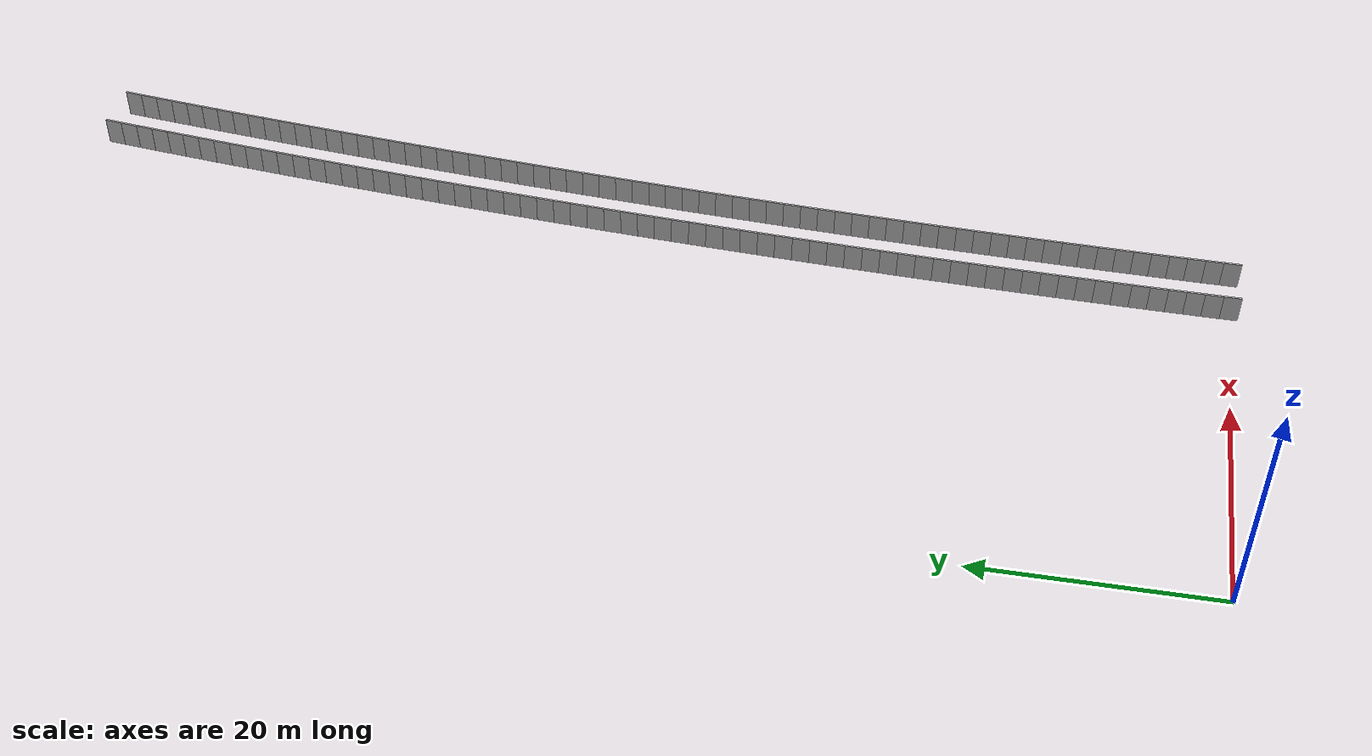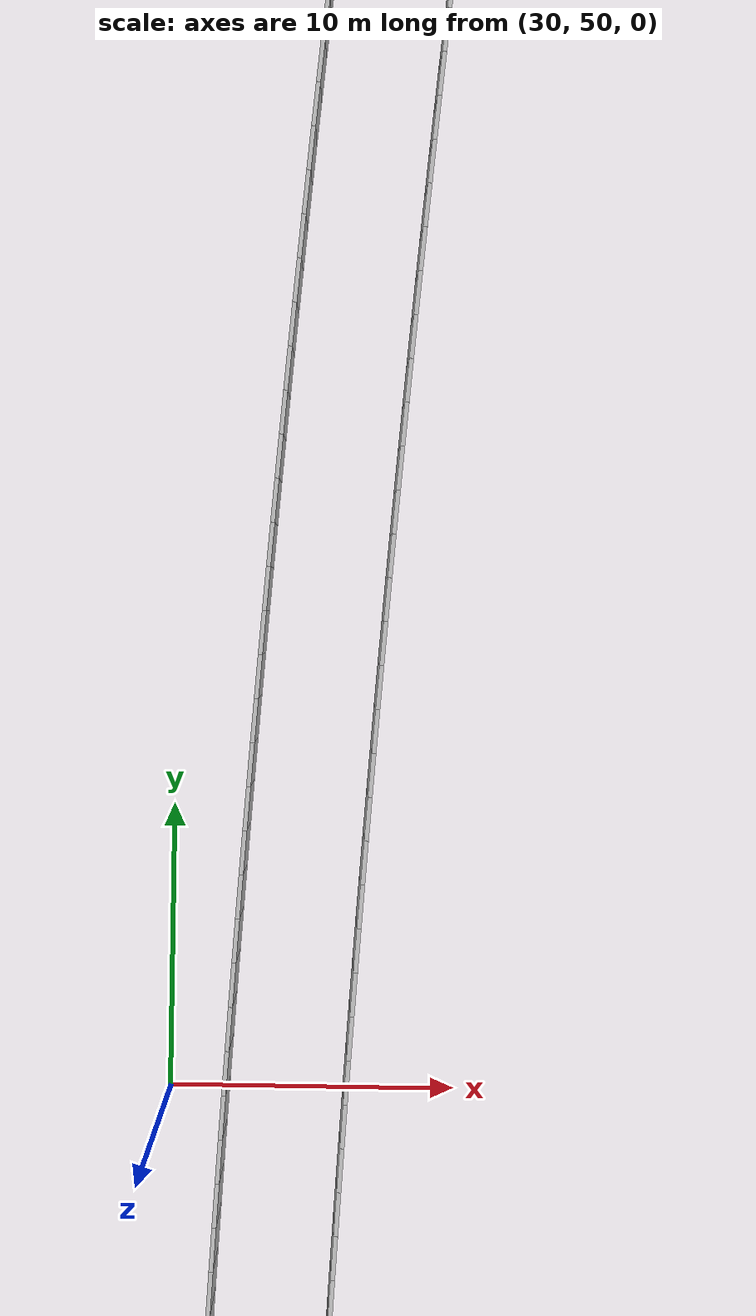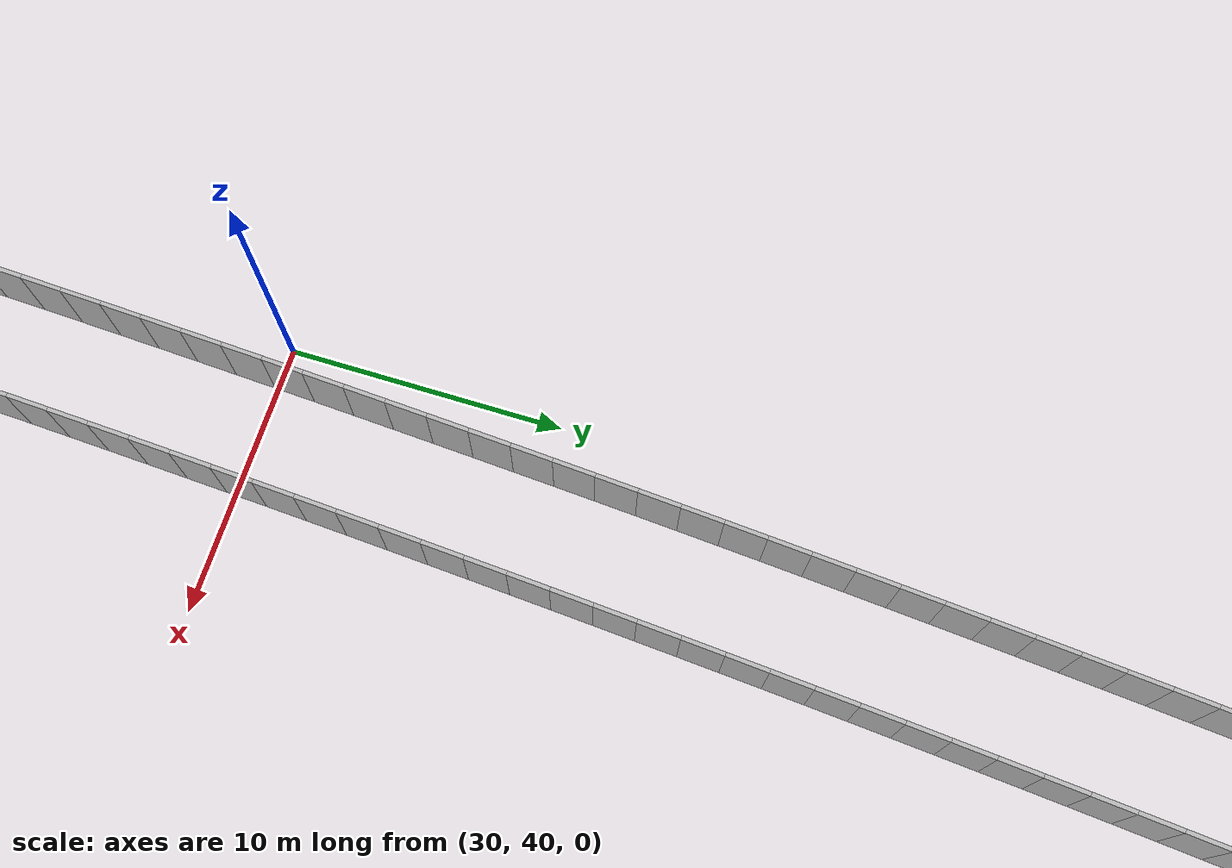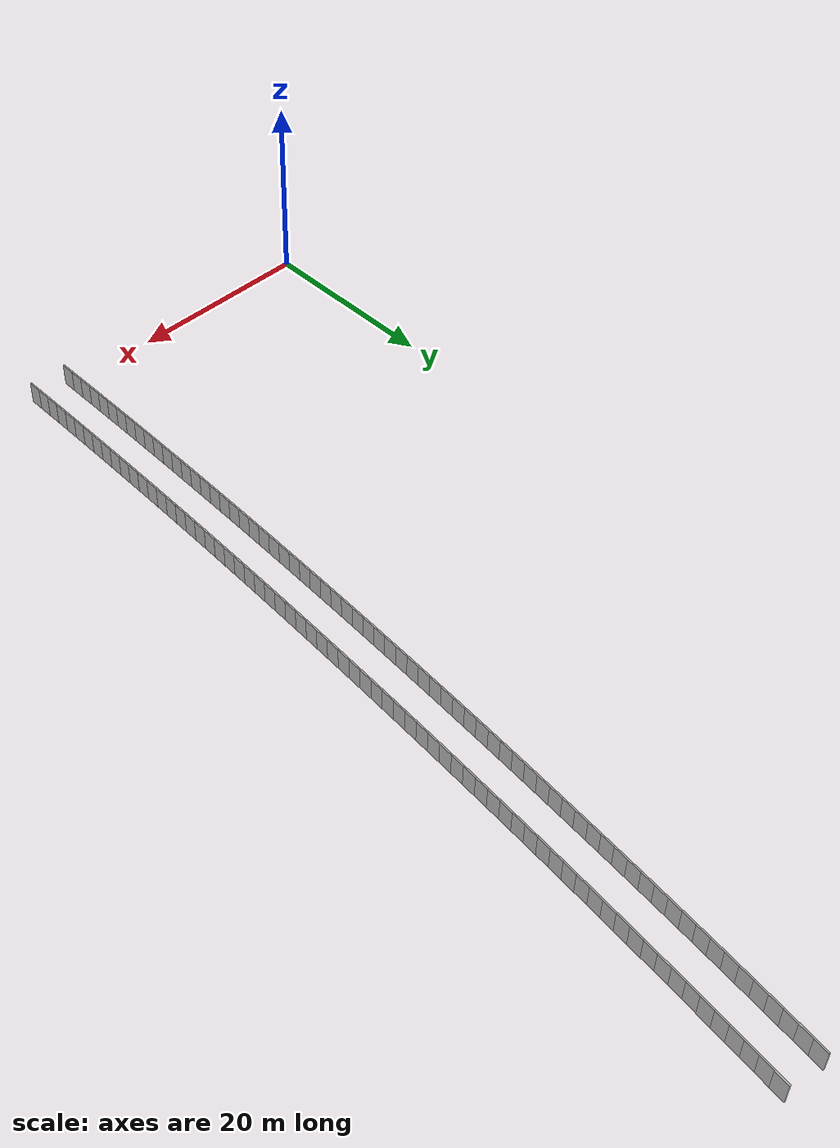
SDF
<?xml version="1.0" ?>
<sdf version="1.6">
  <model name="sps_0113">
    <pose frame="">0 0 0 0 -0 0</pose>
    <static>1</static>
    <self_collide>0</self_collide>
    <allow_auto_disable>0</allow_auto_disable>
    <link name="Wall5177">
      <kinematic>0</kinematic>
      <gravity>1</gravity>
      <self_collide>0</self_collide>
      <collision name="collision">
        <geometry>
          <box>
            <size>1.49644 0.15 2.5</size>
          </box>
        </geometry>
        <pose frame="">0 0 0 0 -0 0</pose>
      </collision>
      <visual name="visual">
        <geometry>
          <box>
            <size>1.49644 0.15 2.5</size>
          </box>
        </geometry>
        <pose frame="">0 0 0 0 -0 0</pose>
        <cast_shadows>1</cast_shadows>
        <transparency>0.0</transparency>
      </visual>
      <pose frame="">40.3633 98.5988 1.25 0 0 -1.68316</pose>
    </link>
    <link name="Wall5178">
      <kinematic>0</kinematic>
      <gravity>1</gravity>
      <self_collide>0</self_collide>
      <collision name="collision">
        <geometry>
          <box>
            <size>1.4966 0.15 2.5</size>
          </box>
        </geometry>
        <pose frame="">0 0 0 0 -0 0</pose>
      </collision>
      <visual name="visual">
        <geometry>
          <box>
            <size>1.4966 0.15 2.5</size>
          </box>
        </geometry>
        <pose frame="">0 0 0 0 -0 0</pose>
        <cast_shadows>1</cast_shadows>
        <transparency>0.0</transparency>
      </visual>
      <pose frame="">40.1967 97.1116 1.25 0 0 -1.68154</pose>
    </link>
    <link name="Wall5179">
      <kinematic>0</kinematic>
      <gravity>1</gravity>
      <self_collide>0</self_collide>
      <collision name="collision">
        <geometry>
          <box>
            <size>1.49672 0.15 2.5</size>
          </box>
        </geometry>
        <pose frame="">0 0 0 0 -0 0</pose>
      </collision>
      <visual name="visual">
        <geometry>
          <box>
            <size>1.49672 0.15 2.5</size>
          </box>
        </geometry>
        <pose frame="">0 0 0 0 -0 0</pose>
        <cast_shadows>1</cast_shadows>
        <transparency>0.0</transparency>
      </visual>
      <pose frame="">40.0324 95.624 1.25 0 0 -1.68006</pose>
    </link>
    <link name="Wall5180">
      <kinematic>0</kinematic>
      <gravity>1</gravity>
      <self_collide>0</self_collide>
      <collision name="collision">
        <geometry>
          <box>
            <size>1.49643 0.15 2.5</size>
          </box>
        </geometry>
        <pose frame="">0 0 0 0 -0 0</pose>
      </collision>
      <visual name="visual">
        <geometry>
          <box>
            <size>1.49643 0.15 2.5</size>
          </box>
        </geometry>
        <pose frame="">0 0 0 0 -0 0</pose>
        <cast_shadows>1</cast_shadows>
        <transparency>0.0</transparency>
      </visual>
      <pose frame="">39.8705 94.1362 1.25 0 0 -1.67831</pose>
    </link>
    <link name="Wall5181">
      <kinematic>0</kinematic>
      <gravity>1</gravity>
      <self_collide>0</self_collide>
      <collision name="collision">
        <geometry>
          <box>
            <size>1.49636 0.15 2.5</size>
          </box>
        </geometry>
        <pose frame="">0 0 0 0 -0 0</pose>
      </collision>
      <visual name="visual">
        <geometry>
          <box>
            <size>1.49636 0.15 2.5</size>
          </box>
        </geometry>
        <pose frame="">0 0 0 0 -0 0</pose>
        <cast_shadows>1</cast_shadows>
        <transparency>0.0</transparency>
      </visual>
      <pose frame="">39.7111 92.6483 1.25 0 0 -1.67672</pose>
    </link>
    <link name="Wall5182">
      <kinematic>0</kinematic>
      <gravity>1</gravity>
      <self_collide>0</self_collide>
      <collision name="collision">
        <geometry>
          <box>
            <size>1.49656 0.15 2.5</size>
          </box>
        </geometry>
        <pose frame="">0 0 0 0 -0 0</pose>
      </collision>
      <visual name="visual">
        <geometry>
          <box>
            <size>1.49656 0.15 2.5</size>
          </box>
        </geometry>
        <pose frame="">0 0 0 0 -0 0</pose>
        <cast_shadows>1</cast_shadows>
        <transparency>0.0</transparency>
      </visual>
      <pose frame="">39.554 91.1601 1.25 0 0 -1.67523</pose>
    </link>
    <link name="Wall5183">
      <kinematic>0</kinematic>
      <gravity>1</gravity>
      <self_collide>0</self_collide>
      <collision name="collision">
        <geometry>
          <box>
            <size>1.49647 0.15 2.5</size>
          </box>
        </geometry>
        <pose frame="">0 0 0 0 -0 0</pose>
      </collision>
      <visual name="visual">
        <geometry>
          <box>
            <size>1.49647 0.15 2.5</size>
          </box>
        </geometry>
        <pose frame="">0 0 0 0 -0 0</pose>
        <cast_shadows>1</cast_shadows>
        <transparency>0.0</transparency>
      </visual>
      <pose frame="">39.3993 89.6716 1.25 0 0 -1.67347</pose>
    </link>
    <link name="Wall5184">
      <kinematic>0</kinematic>
      <gravity>1</gravity>
      <self_collide>0</self_collide>
      <collision name="collision">
        <geometry>
          <box>
            <size>1.49651 0.15 2.5</size>
          </box>
        </geometry>
        <pose frame="">0 0 0 0 -0 0</pose>
      </collision>
      <visual name="visual">
        <geometry>
          <box>
            <size>1.49651 0.15 2.5</size>
          </box>
        </geometry>
        <pose frame="">0 0 0 0 -0 0</pose>
        <cast_shadows>1</cast_shadows>
        <transparency>0.0</transparency>
      </visual>
      <pose frame="">39.2469 88.1829 1.25 0 0 -1.67216</pose>
    </link>
    <link name="Wall5185">
      <kinematic>0</kinematic>
      <gravity>1</gravity>
      <self_collide>0</self_collide>
      <collision name="collision">
        <geometry>
          <box>
            <size>1.49661 0.15 2.5</size>
          </box>
        </geometry>
        <pose frame="">0 0 0 0 -0 0</pose>
      </collision>
      <visual name="visual">
        <geometry>
          <box>
            <size>1.49661 0.15 2.5</size>
          </box>
        </geometry>
        <pose frame="">0 0 0 0 -0 0</pose>
        <cast_shadows>1</cast_shadows>
        <transparency>0.0</transparency>
      </visual>
      <pose frame="">39.0969 86.6939 1.25 0 0 -1.67035</pose>
    </link>
    <link name="Wall5186">
      <kinematic>0</kinematic>
      <gravity>1</gravity>
      <self_collide>0</self_collide>
      <collision name="collision">
        <geometry>
          <box>
            <size>1.4964 0.15 2.5</size>
          </box>
        </geometry>
        <pose frame="">0 0 0 0 -0 0</pose>
      </collision>
      <visual name="visual">
        <geometry>
          <box>
            <size>1.4964 0.15 2.5</size>
          </box>
        </geometry>
        <pose frame="">0 0 0 0 -0 0</pose>
        <cast_shadows>1</cast_shadows>
        <transparency>0.0</transparency>
      </visual>
      <pose frame="">38.9492 85.2047 1.25 0 0 -1.66893</pose>
    </link>
    <link name="Wall5187">
      <kinematic>0</kinematic>
      <gravity>1</gravity>
      <self_collide>0</self_collide>
      <collision name="collision">
        <geometry>
          <box>
            <size>1.49657 0.15 2.5</size>
          </box>
        </geometry>
        <pose frame="">0 0 0 0 -0 0</pose>
      </collision>
      <visual name="visual">
        <geometry>
          <box>
            <size>1.49657 0.15 2.5</size>
          </box>
        </geometry>
        <pose frame="">0 0 0 0 -0 0</pose>
        <cast_shadows>1</cast_shadows>
        <transparency>0.0</transparency>
      </visual>
      <pose frame="">38.8039 83.7153 1.25 0 0 -1.66719</pose>
    </link>
    <link name="Wall5188">
      <kinematic>0</kinematic>
      <gravity>1</gravity>
      <self_collide>0</self_collide>
      <collision name="collision">
        <geometry>
          <box>
            <size>1.49656 0.15 2.5</size>
          </box>
        </geometry>
        <pose frame="">0 0 0 0 -0 0</pose>
      </collision>
      <visual name="visual">
        <geometry>
          <box>
            <size>1.49656 0.15 2.5</size>
          </box>
        </geometry>
        <pose frame="">0 0 0 0 -0 0</pose>
        <cast_shadows>1</cast_shadows>
        <transparency>0.0</transparency>
      </visual>
      <pose frame="">38.6608 82.2256 1.25 0 0 -1.6658</pose>
    </link>
    <link name="Wall5189">
      <kinematic>0</kinematic>
      <gravity>1</gravity>
      <self_collide>0</self_collide>
      <collision name="collision">
        <geometry>
          <box>
            <size>1.4965 0.15 2.5</size>
          </box>
        </geometry>
        <pose frame="">0 0 0 0 -0 0</pose>
      </collision>
      <visual name="visual">
        <geometry>
          <box>
            <size>1.4965 0.15 2.5</size>
          </box>
        </geometry>
        <pose frame="">0 0 0 0 -0 0</pose>
        <cast_shadows>1</cast_shadows>
        <transparency>0.0</transparency>
      </visual>
      <pose frame="">38.5202 80.7357 1.25 0 0 -1.66409</pose>
    </link>
    <link name="Wall5190">
      <kinematic>0</kinematic>
      <gravity>1</gravity>
      <self_collide>0</self_collide>
      <collision name="collision">
        <geometry>
          <box>
            <size>1.49648 0.15 2.5</size>
          </box>
        </geometry>
        <pose frame="">0 0 0 0 -0 0</pose>
      </collision>
      <visual name="visual">
        <geometry>
          <box>
            <size>1.49648 0.15 2.5</size>
          </box>
        </geometry>
        <pose frame="">0 0 0 0 -0 0</pose>
        <cast_shadows>1</cast_shadows>
        <transparency>0.0</transparency>
      </visual>
      <pose frame="">38.3819 79.2456 1.25 0 0 -1.66261</pose>
    </link>
    <link name="Wall5191">
      <kinematic>0</kinematic>
      <gravity>1</gravity>
      <self_collide>0</self_collide>
      <collision name="collision">
        <geometry>
          <box>
            <size>1.4965 0.15 2.5</size>
          </box>
        </geometry>
        <pose frame="">0 0 0 0 -0 0</pose>
      </collision>
      <visual name="visual">
        <geometry>
          <box>
            <size>1.4965 0.15 2.5</size>
          </box>
        </geometry>
        <pose frame="">0 0 0 0 -0 0</pose>
        <cast_shadows>1</cast_shadows>
        <transparency>0.0</transparency>
      </visual>
      <pose frame="">38.2458 77.7553 1.25 0 0 -1.66101</pose>
    </link>
    <link name="Wall5192">
      <kinematic>0</kinematic>
      <gravity>1</gravity>
      <self_collide>0</self_collide>
      <collision name="collision">
        <geometry>
          <box>
            <size>1.49663 0.15 2.5</size>
          </box>
        </geometry>
        <pose frame="">0 0 0 0 -0 0</pose>
      </collision>
      <visual name="visual">
        <geometry>
          <box>
            <size>1.49663 0.15 2.5</size>
          </box>
        </geometry>
        <pose frame="">0 0 0 0 -0 0</pose>
        <cast_shadows>1</cast_shadows>
        <transparency>0.0</transparency>
      </visual>
      <pose frame="">38.1123 76.2647 1.25 0 0 -1.65924</pose>
    </link>
    <link name="Wall5193">
      <kinematic>0</kinematic>
      <gravity>1</gravity>
      <self_collide>0</self_collide>
      <collision name="collision">
        <geometry>
          <box>
            <size>1.49644 0.15 2.5</size>
          </box>
        </geometry>
        <pose frame="">0 0 0 0 -0 0</pose>
      </collision>
      <visual name="visual">
        <geometry>
          <box>
            <size>1.49644 0.15 2.5</size>
          </box>
        </geometry>
        <pose frame="">0 0 0 0 -0 0</pose>
        <cast_shadows>1</cast_shadows>
        <transparency>0.0</transparency>
      </visual>
      <pose frame="">37.9813 74.7739 1.25 0 0 -1.65774</pose>
    </link>
    <link name="Wall5194">
      <kinematic>0</kinematic>
      <gravity>1</gravity>
      <self_collide>0</self_collide>
      <collision name="collision">
        <geometry>
          <box>
            <size>1.4965 0.15 2.5</size>
          </box>
        </geometry>
        <pose frame="">0 0 0 0 -0 0</pose>
      </collision>
      <visual name="visual">
        <geometry>
          <box>
            <size>1.4965 0.15 2.5</size>
          </box>
        </geometry>
        <pose frame="">0 0 0 0 -0 0</pose>
        <cast_shadows>1</cast_shadows>
        <transparency>0.0</transparency>
      </visual>
      <pose frame="">37.8524 73.283 1.25 0 0 -1.65631</pose>
    </link>
    <link name="Wall5195">
      <kinematic>0</kinematic>
      <gravity>1</gravity>
      <self_collide>0</self_collide>
      <collision name="collision">
        <geometry>
          <box>
            <size>1.49664 0.15 2.5</size>
          </box>
        </geometry>
        <pose frame="">0 0 0 0 -0 0</pose>
      </collision>
      <visual name="visual">
        <geometry>
          <box>
            <size>1.49664 0.15 2.5</size>
          </box>
        </geometry>
        <pose frame="">0 0 0 0 -0 0</pose>
        <cast_shadows>1</cast_shadows>
        <transparency>0.0</transparency>
      </visual>
      <pose frame="">37.7259 71.7918 1.25 0 0 -1.65458</pose>
    </link>
    <link name="Wall5196">
      <kinematic>0</kinematic>
      <gravity>1</gravity>
      <self_collide>0</self_collide>
      <collision name="collision">
        <geometry>
          <box>
            <size>1.49644 0.15 2.5</size>
          </box>
        </geometry>
        <pose frame="">0 0 0 0 -0 0</pose>
      </collision>
      <visual name="visual">
        <geometry>
          <box>
            <size>1.49644 0.15 2.5</size>
          </box>
        </geometry>
        <pose frame="">0 0 0 0 -0 0</pose>
        <cast_shadows>1</cast_shadows>
        <transparency>0.0</transparency>
      </visual>
      <pose frame="">37.6018 70.3004 1.25 0 0 -1.65295</pose>
    </link>
    <link name="Wall5197">
      <kinematic>0</kinematic>
      <gravity>1</gravity>
      <self_collide>0</self_collide>
      <collision name="collision">
        <geometry>
          <box>
            <size>1.49667 0.15 2.5</size>
          </box>
        </geometry>
        <pose frame="">0 0 0 0 -0 0</pose>
      </collision>
      <visual name="visual">
        <geometry>
          <box>
            <size>1.49667 0.15 2.5</size>
          </box>
        </geometry>
        <pose frame="">0 0 0 0 -0 0</pose>
        <cast_shadows>1</cast_shadows>
        <transparency>0.0</transparency>
      </visual>
      <pose frame="">37.4802 68.8088 1.25 0 0 -1.6513</pose>
    </link>
    <link name="Wall5198">
      <kinematic>0</kinematic>
      <gravity>1</gravity>
      <self_collide>0</self_collide>
      <collision name="collision">
        <geometry>
          <box>
            <size>1.49644 0.15 2.5</size>
          </box>
        </geometry>
        <pose frame="">0 0 0 0 -0 0</pose>
      </collision>
      <visual name="visual">
        <geometry>
          <box>
            <size>1.49644 0.15 2.5</size>
          </box>
        </geometry>
        <pose frame="">0 0 0 0 -0 0</pose>
        <cast_shadows>1</cast_shadows>
        <transparency>0.0</transparency>
      </visual>
      <pose frame="">37.361 67.317 1.25 0 0 -1.64988</pose>
    </link>
    <link name="Wall5199">
      <kinematic>0</kinematic>
      <gravity>1</gravity>
      <self_collide>0</self_collide>
      <collision name="collision">
        <geometry>
          <box>
            <size>1.4965 0.15 2.5</size>
          </box>
        </geometry>
        <pose frame="">0 0 0 0 -0 0</pose>
      </collision>
      <visual name="visual">
        <geometry>
          <box>
            <size>1.4965 0.15 2.5</size>
          </box>
        </geometry>
        <pose frame="">0 0 0 0 -0 0</pose>
        <cast_shadows>1</cast_shadows>
        <transparency>0.0</transparency>
      </visual>
      <pose frame="">37.2439 65.8251 1.25 0 0 -1.64837</pose>
    </link>
    <link name="Wall5200">
      <kinematic>0</kinematic>
      <gravity>1</gravity>
      <self_collide>0</self_collide>
      <collision name="collision">
        <geometry>
          <box>
            <size>1.49655 0.15 2.5</size>
          </box>
        </geometry>
        <pose frame="">0 0 0 0 -0 0</pose>
      </collision>
      <visual name="visual">
        <geometry>
          <box>
            <size>1.49655 0.15 2.5</size>
          </box>
        </geometry>
        <pose frame="">0 0 0 0 -0 0</pose>
        <cast_shadows>1</cast_shadows>
        <transparency>0.0</transparency>
      </visual>
      <pose frame="">37.1292 64.333 1.25 0 0 -1.64665</pose>
    </link>
    <link name="Wall5201">
      <kinematic>0</kinematic>
      <gravity>1</gravity>
      <self_collide>0</self_collide>
      <collision name="collision">
        <geometry>
          <box>
            <size>1.49651 0.15 2.5</size>
          </box>
        </geometry>
        <pose frame="">0 0 0 0 -0 0</pose>
      </collision>
      <visual name="visual">
        <geometry>
          <box>
            <size>1.49651 0.15 2.5</size>
          </box>
        </geometry>
        <pose frame="">0 0 0 0 -0 0</pose>
        <cast_shadows>1</cast_shadows>
        <transparency>0.0</transparency>
      </visual>
      <pose frame="">37.0169 62.8407 1.25 0 0 -1.64518</pose>
    </link>
    <link name="Wall5202">
      <kinematic>0</kinematic>
      <gravity>1</gravity>
      <self_collide>0</self_collide>
      <collision name="collision">
        <geometry>
          <box>
            <size>1.49656 0.15 2.5</size>
          </box>
        </geometry>
        <pose frame="">0 0 0 0 -0 0</pose>
      </collision>
      <visual name="visual">
        <geometry>
          <box>
            <size>1.49656 0.15 2.5</size>
          </box>
        </geometry>
        <pose frame="">0 0 0 0 -0 0</pose>
        <cast_shadows>1</cast_shadows>
        <transparency>0.0</transparency>
      </visual>
      <pose frame="">36.907 61.3482 1.25 0 0 -1.64341</pose>
    </link>
    <link name="Wall5203">
      <kinematic>0</kinematic>
      <gravity>1</gravity>
      <self_collide>0</self_collide>
      <collision name="collision">
        <geometry>
          <box>
            <size>1.49641 0.15 2.5</size>
          </box>
        </geometry>
        <pose frame="">0 0 0 0 -0 0</pose>
      </collision>
      <visual name="visual">
        <geometry>
          <box>
            <size>1.49641 0.15 2.5</size>
          </box>
        </geometry>
        <pose frame="">0 0 0 0 -0 0</pose>
        <cast_shadows>1</cast_shadows>
        <transparency>0.0</transparency>
      </visual>
      <pose frame="">36.7995 59.8556 1.25 0 0 -1.64199</pose>
    </link>
    <link name="Wall5204">
      <kinematic>0</kinematic>
      <gravity>1</gravity>
      <self_collide>0</self_collide>
      <collision name="collision">
        <geometry>
          <box>
            <size>1.4966 0.15 2.5</size>
          </box>
        </geometry>
        <pose frame="">0 0 0 0 -0 0</pose>
      </collision>
      <visual name="visual">
        <geometry>
          <box>
            <size>1.4966 0.15 2.5</size>
          </box>
        </geometry>
        <pose frame="">0 0 0 0 -0 0</pose>
        <cast_shadows>1</cast_shadows>
        <transparency>0.0</transparency>
      </visual>
      <pose frame="">36.6942 58.3628 1.25 0 0 -1.64035</pose>
    </link>
    <link name="Wall5205">
      <kinematic>0</kinematic>
      <gravity>1</gravity>
      <self_collide>0</self_collide>
      <collision name="collision">
        <geometry>
          <box>
            <size>1.49643 0.15 2.5</size>
          </box>
        </geometry>
        <pose frame="">0 0 0 0 -0 0</pose>
      </collision>
      <visual name="visual">
        <geometry>
          <box>
            <size>1.49643 0.15 2.5</size>
          </box>
        </geometry>
        <pose frame="">0 0 0 0 -0 0</pose>
        <cast_shadows>1</cast_shadows>
        <transparency>0.0</transparency>
      </visual>
      <pose frame="">36.5915 56.8698 1.25 0 0 -1.63872</pose>
    </link>
    <link name="Wall5206">
      <kinematic>0</kinematic>
      <gravity>1</gravity>
      <self_collide>0</self_collide>
      <collision name="collision">
        <geometry>
          <box>
            <size>1.49652 0.15 2.5</size>
          </box>
        </geometry>
        <pose frame="">0 0 0 0 -0 0</pose>
      </collision>
      <visual name="visual">
        <geometry>
          <box>
            <size>1.49652 0.15 2.5</size>
          </box>
        </geometry>
        <pose frame="">0 0 0 0 -0 0</pose>
        <cast_shadows>1</cast_shadows>
        <transparency>0.0</transparency>
      </visual>
      <pose frame="">36.4911 55.3767 1.25 0 0 -1.63716</pose>
    </link>
    <link name="Wall5207">
      <kinematic>0</kinematic>
      <gravity>1</gravity>
      <self_collide>0</self_collide>
      <collision name="collision">
        <geometry>
          <box>
            <size>1.49655 0.15 2.5</size>
          </box>
        </geometry>
        <pose frame="">0 0 0 0 -0 0</pose>
      </collision>
      <visual name="visual">
        <geometry>
          <box>
            <size>1.49655 0.15 2.5</size>
          </box>
        </geometry>
        <pose frame="">0 0 0 0 -0 0</pose>
        <cast_shadows>1</cast_shadows>
        <transparency>0.0</transparency>
      </visual>
      <pose frame="">36.3929 53.8834 1.25 0 0 -1.63565</pose>
    </link>
    <link name="Wall5208">
      <kinematic>0</kinematic>
      <gravity>1</gravity>
      <self_collide>0</self_collide>
      <collision name="collision">
        <geometry>
          <box>
            <size>1.49658 0.15 2.5</size>
          </box>
        </geometry>
        <pose frame="">0 0 0 0 -0 0</pose>
      </collision>
      <visual name="visual">
        <geometry>
          <box>
            <size>1.49658 0.15 2.5</size>
          </box>
        </geometry>
        <pose frame="">0 0 0 0 -0 0</pose>
        <cast_shadows>1</cast_shadows>
        <transparency>0.0</transparency>
      </visual>
      <pose frame="">36.2971 52.3899 1.25 0 0 -1.63405</pose>
    </link>
    <link name="Wall5209">
      <kinematic>0</kinematic>
      <gravity>1</gravity>
      <self_collide>0</self_collide>
      <collision name="collision">
        <geometry>
          <box>
            <size>1.49642 0.15 2.5</size>
          </box>
        </geometry>
        <pose frame="">0 0 0 0 -0 0</pose>
      </collision>
      <visual name="visual">
        <geometry>
          <box>
            <size>1.49642 0.15 2.5</size>
          </box>
        </geometry>
        <pose frame="">0 0 0 0 -0 0</pose>
        <cast_shadows>1</cast_shadows>
        <transparency>0.0</transparency>
      </visual>
      <pose frame="">36.2038 50.8963 1.25 0 0 -1.6323</pose>
    </link>
    <link name="Wall5210">
      <kinematic>0</kinematic>
      <gravity>1</gravity>
      <self_collide>0</self_collide>
      <collision name="collision">
        <geometry>
          <box>
            <size>1.49648 0.15 2.5</size>
          </box>
        </geometry>
        <pose frame="">0 0 0 0 -0 0</pose>
      </collision>
      <visual name="visual">
        <geometry>
          <box>
            <size>1.49648 0.15 2.5</size>
          </box>
        </geometry>
        <pose frame="">0 0 0 0 -0 0</pose>
        <cast_shadows>1</cast_shadows>
        <transparency>0.0</transparency>
      </visual>
      <pose frame="">36.1128 49.4026 1.25 0 0 -1.63099</pose>
    </link>
    <link name="Wall5211">
      <kinematic>0</kinematic>
      <gravity>1</gravity>
      <self_collide>0</self_collide>
      <collision name="collision">
        <geometry>
          <box>
            <size>1.49657 0.15 2.5</size>
          </box>
        </geometry>
        <pose frame="">0 0 0 0 -0 0</pose>
      </collision>
      <visual name="visual">
        <geometry>
          <box>
            <size>1.49657 0.15 2.5</size>
          </box>
        </geometry>
        <pose frame="">0 0 0 0 -0 0</pose>
        <cast_shadows>1</cast_shadows>
        <transparency>0.0</transparency>
      </visual>
      <pose frame="">36.0241 47.9087 1.25 0 0 -1.62923</pose>
    </link>
    <link name="Wall5212">
      <kinematic>0</kinematic>
      <gravity>1</gravity>
      <self_collide>0</self_collide>
      <collision name="collision">
        <geometry>
          <box>
            <size>1.49643 0.15 2.5</size>
          </box>
        </geometry>
        <pose frame="">0 0 0 0 -0 0</pose>
      </collision>
      <visual name="visual">
        <geometry>
          <box>
            <size>1.49643 0.15 2.5</size>
          </box>
        </geometry>
        <pose frame="">0 0 0 0 -0 0</pose>
        <cast_shadows>1</cast_shadows>
        <transparency>0.0</transparency>
      </visual>
      <pose frame="">35.9379 46.4147 1.25 0 0 -1.6276</pose>
    </link>
    <link name="Wall5213">
      <kinematic>0</kinematic>
      <gravity>1</gravity>
      <self_collide>0</self_collide>
      <collision name="collision">
        <geometry>
          <box>
            <size>1.4965 0.15 2.5</size>
          </box>
        </geometry>
        <pose frame="">0 0 0 0 -0 0</pose>
      </collision>
      <visual name="visual">
        <geometry>
          <box>
            <size>1.4965 0.15 2.5</size>
          </box>
        </geometry>
        <pose frame="">0 0 0 0 -0 0</pose>
        <cast_shadows>1</cast_shadows>
        <transparency>0.0</transparency>
      </visual>
      <pose frame="">35.8541 44.9206 1.25 0 0 -1.62617</pose>
    </link>
    <link name="Wall5214">
      <kinematic>0</kinematic>
      <gravity>1</gravity>
      <self_collide>0</self_collide>
      <collision name="collision">
        <geometry>
          <box>
            <size>1.49672 0.15 2.5</size>
          </box>
        </geometry>
        <pose frame="">0 0 0 0 -0 0</pose>
      </collision>
      <visual name="visual">
        <geometry>
          <box>
            <size>1.49672 0.15 2.5</size>
          </box>
        </geometry>
        <pose frame="">0 0 0 0 -0 0</pose>
        <cast_shadows>1</cast_shadows>
        <transparency>0.0</transparency>
      </visual>
      <pose frame="">35.7725 43.4262 1.25 0 0 -1.62441</pose>
    </link>
    <link name="Wall5215">
      <kinematic>0</kinematic>
      <gravity>1</gravity>
      <self_collide>0</self_collide>
      <collision name="collision">
        <geometry>
          <box>
            <size>1.49648 0.15 2.5</size>
          </box>
        </geometry>
        <pose frame="">0 0 0 0 -0 0</pose>
      </collision>
      <visual name="visual">
        <geometry>
          <box>
            <size>1.49648 0.15 2.5</size>
          </box>
        </geometry>
        <pose frame="">0 0 0 0 -0 0</pose>
        <cast_shadows>1</cast_shadows>
        <transparency>0.0</transparency>
      </visual>
      <pose frame="">35.6934 41.9317 1.25 0 0 -1.62294</pose>
    </link>
    <link name="Wall5216">
      <kinematic>0</kinematic>
      <gravity>1</gravity>
      <self_collide>0</self_collide>
      <collision name="collision">
        <geometry>
          <box>
            <size>1.49648 0.15 2.5</size>
          </box>
        </geometry>
        <pose frame="">0 0 0 0 -0 0</pose>
      </collision>
      <visual name="visual">
        <geometry>
          <box>
            <size>1.49648 0.15 2.5</size>
          </box>
        </geometry>
        <pose frame="">0 0 0 0 -0 0</pose>
        <cast_shadows>1</cast_shadows>
        <transparency>0.0</transparency>
      </visual>
      <pose frame="">35.6167 40.4372 1.25 0 0 -1.62131</pose>
    </link>
    <link name="Wall5217">
      <kinematic>0</kinematic>
      <gravity>1</gravity>
      <self_collide>0</self_collide>
      <collision name="collision">
        <geometry>
          <box>
            <size>1.49642 0.15 2.5</size>
          </box>
        </geometry>
        <pose frame="">0 0 0 0 -0 0</pose>
      </collision>
      <visual name="visual">
        <geometry>
          <box>
            <size>1.49642 0.15 2.5</size>
          </box>
        </geometry>
        <pose frame="">0 0 0 0 -0 0</pose>
        <cast_shadows>1</cast_shadows>
        <transparency>0.0</transparency>
      </visual>
      <pose frame="">35.5423 38.9426 1.25 0 0 -1.61976</pose>
    </link>
    <link name="Wall5218">
      <kinematic>0</kinematic>
      <gravity>1</gravity>
      <self_collide>0</self_collide>
      <collision name="collision">
        <geometry>
          <box>
            <size>1.49644 0.15 2.5</size>
          </box>
        </geometry>
        <pose frame="">0 0 0 0 -0 0</pose>
      </collision>
      <visual name="visual">
        <geometry>
          <box>
            <size>1.49644 0.15 2.5</size>
          </box>
        </geometry>
        <pose frame="">0 0 0 0 -0 0</pose>
        <cast_shadows>1</cast_shadows>
        <transparency>0.0</transparency>
      </visual>
      <pose frame="">35.4701 37.4479 1.25 0 0 -1.61825</pose>
    </link>
    <link name="Wall5219">
      <kinematic>0</kinematic>
      <gravity>1</gravity>
      <self_collide>0</self_collide>
      <collision name="collision">
        <geometry>
          <box>
            <size>1.49656 0.15 2.5</size>
          </box>
        </geometry>
        <pose frame="">0 0 0 0 -0 0</pose>
      </collision>
      <visual name="visual">
        <geometry>
          <box>
            <size>1.49656 0.15 2.5</size>
          </box>
        </geometry>
        <pose frame="">0 0 0 0 -0 0</pose>
        <cast_shadows>1</cast_shadows>
        <transparency>0.0</transparency>
      </visual>
      <pose frame="">35.4004 35.953 1.25 0 0 -1.61653</pose>
    </link>
    <link name="Wall5220">
      <kinematic>0</kinematic>
      <gravity>1</gravity>
      <self_collide>0</self_collide>
      <collision name="collision">
        <geometry>
          <box>
            <size>1.4967 0.15 2.5</size>
          </box>
        </geometry>
        <pose frame="">0 0 0 0 -0 0</pose>
      </collision>
      <visual name="visual">
        <geometry>
          <box>
            <size>1.4967 0.15 2.5</size>
          </box>
        </geometry>
        <pose frame="">0 0 0 0 -0 0</pose>
        <cast_shadows>1</cast_shadows>
        <transparency>0.0</transparency>
      </visual>
      <pose frame="">35.3332 34.4579 1.25 0 0 -1.61502</pose>
    </link>
    <link name="Wall5221">
      <kinematic>0</kinematic>
      <gravity>1</gravity>
      <self_collide>0</self_collide>
      <collision name="collision">
        <geometry>
          <box>
            <size>1.49636 0.15 2.5</size>
          </box>
        </geometry>
        <pose frame="">0 0 0 0 -0 0</pose>
      </collision>
      <visual name="visual">
        <geometry>
          <box>
            <size>1.49636 0.15 2.5</size>
          </box>
        </geometry>
        <pose frame="">0 0 0 0 -0 0</pose>
        <cast_shadows>1</cast_shadows>
        <transparency>0.0</transparency>
      </visual>
      <pose frame="">35.2681 32.9628 1.25 0 0 -1.61347</pose>
    </link>
    <link name="Wall5222">
      <kinematic>0</kinematic>
      <gravity>1</gravity>
      <self_collide>0</self_collide>
      <collision name="collision">
        <geometry>
          <box>
            <size>1.49668 0.15 2.5</size>
          </box>
        </geometry>
        <pose frame="">0 0 0 0 -0 0</pose>
      </collision>
      <visual name="visual">
        <geometry>
          <box>
            <size>1.49668 0.15 2.5</size>
          </box>
        </geometry>
        <pose frame="">0 0 0 0 -0 0</pose>
        <cast_shadows>1</cast_shadows>
        <transparency>0.0</transparency>
      </visual>
      <pose frame="">35.2055 31.4676 1.25 0 0 -1.61183</pose>
    </link>
    <link name="Wall5223">
      <kinematic>0</kinematic>
      <gravity>1</gravity>
      <self_collide>0</self_collide>
      <collision name="collision">
        <geometry>
          <box>
            <size>1.49633 0.15 2.5</size>
          </box>
        </geometry>
        <pose frame="">0 0 0 0 -0 0</pose>
      </collision>
      <visual name="visual">
        <geometry>
          <box>
            <size>1.49633 0.15 2.5</size>
          </box>
        </geometry>
        <pose frame="">0 0 0 0 -0 0</pose>
        <cast_shadows>1</cast_shadows>
        <transparency>0.0</transparency>
      </visual>
      <pose frame="">35.1454 29.9723 1.25 0 0 -1.61009</pose>
    </link>
    <link name="Wall5224">
      <kinematic>0</kinematic>
      <gravity>1</gravity>
      <self_collide>0</self_collide>
      <collision name="collision">
        <geometry>
          <box>
            <size>1.49668 0.15 2.5</size>
          </box>
        </geometry>
        <pose frame="">0 0 0 0 -0 0</pose>
      </collision>
      <visual name="visual">
        <geometry>
          <box>
            <size>1.49668 0.15 2.5</size>
          </box>
        </geometry>
        <pose frame="">0 0 0 0 -0 0</pose>
        <cast_shadows>1</cast_shadows>
        <transparency>0.0</transparency>
      </visual>
      <pose frame="">35.0876 28.4769 1.25 0 0 -1.60877</pose>
    </link>
    <link name="Wall5225">
      <kinematic>0</kinematic>
      <gravity>1</gravity>
      <self_collide>0</self_collide>
      <collision name="collision">
        <geometry>
          <box>
            <size>1.49659 0.15 2.5</size>
          </box>
        </geometry>
        <pose frame="">0 0 0 0 -0 0</pose>
      </collision>
      <visual name="visual">
        <geometry>
          <box>
            <size>1.49659 0.15 2.5</size>
          </box>
        </geometry>
        <pose frame="">0 0 0 0 -0 0</pose>
        <cast_shadows>1</cast_shadows>
        <transparency>0.0</transparency>
      </visual>
      <pose frame="">35.0321 26.9813 1.25 0 0 -1.60702</pose>
    </link>
    <link name="Wall5226">
      <kinematic>0</kinematic>
      <gravity>1</gravity>
      <self_collide>0</self_collide>
      <collision name="collision">
        <geometry>
          <box>
            <size>1.4965 0.15 2.5</size>
          </box>
        </geometry>
        <pose frame="">0 0 0 0 -0 0</pose>
      </collision>
      <visual name="visual">
        <geometry>
          <box>
            <size>1.4965 0.15 2.5</size>
          </box>
        </geometry>
        <pose frame="">0 0 0 0 -0 0</pose>
        <cast_shadows>1</cast_shadows>
        <transparency>0.0</transparency>
      </visual>
      <pose frame="">34.9791 25.4857 1.25 0 0 -1.60539</pose>
    </link>
    <link name="Wall5227">
      <kinematic>0</kinematic>
      <gravity>1</gravity>
      <self_collide>0</self_collide>
      <collision name="collision">
        <geometry>
          <box>
            <size>1.49661 0.15 2.5</size>
          </box>
        </geometry>
        <pose frame="">0 0 0 0 -0 0</pose>
      </collision>
      <visual name="visual">
        <geometry>
          <box>
            <size>1.49661 0.15 2.5</size>
          </box>
        </geometry>
        <pose frame="">0 0 0 0 -0 0</pose>
        <cast_shadows>1</cast_shadows>
        <transparency>0.0</transparency>
      </visual>
      <pose frame="">34.9285 23.99 1.25 0 0 -1.60396</pose>
    </link>
    <link name="Wall5228">
      <kinematic>0</kinematic>
      <gravity>1</gravity>
      <self_collide>0</self_collide>
      <collision name="collision">
        <geometry>
          <box>
            <size>1.49635 0.15 2.5</size>
          </box>
        </geometry>
        <pose frame="">0 0 0 0 -0 0</pose>
      </collision>
      <visual name="visual">
        <geometry>
          <box>
            <size>1.49635 0.15 2.5</size>
          </box>
        </geometry>
        <pose frame="">0 0 0 0 -0 0</pose>
        <cast_shadows>1</cast_shadows>
        <transparency>0.0</transparency>
      </visual>
      <pose frame="">34.8801 22.4943 1.25 0 0 -1.60233</pose>
    </link>
    <link name="Wall5229">
      <kinematic>0</kinematic>
      <gravity>1</gravity>
      <self_collide>0</self_collide>
      <collision name="collision">
        <geometry>
          <box>
            <size>1.49646 0.15 2.5</size>
          </box>
        </geometry>
        <pose frame="">0 0 0 0 -0 0</pose>
      </collision>
      <visual name="visual">
        <geometry>
          <box>
            <size>1.49646 0.15 2.5</size>
          </box>
        </geometry>
        <pose frame="">0 0 0 0 -0 0</pose>
        <cast_shadows>1</cast_shadows>
        <transparency>0.0</transparency>
      </visual>
      <pose frame="">34.8341 20.9986 1.25 0 0 -1.60074</pose>
    </link>
    <link name="Wall5230">
      <kinematic>0</kinematic>
      <gravity>1</gravity>
      <self_collide>0</self_collide>
      <collision name="collision">
        <geometry>
          <box>
            <size>1.49639 0.15 2.5</size>
          </box>
        </geometry>
        <pose frame="">0 0 0 0 -0 0</pose>
      </collision>
      <visual name="visual">
        <geometry>
          <box>
            <size>1.49639 0.15 2.5</size>
          </box>
        </geometry>
        <pose frame="">0 0 0 0 -0 0</pose>
        <cast_shadows>1</cast_shadows>
        <transparency>0.0</transparency>
      </visual>
      <pose frame="">34.7905 19.5028 1.25 0 0 -1.59915</pose>
    </link>
    <link name="Wall5231">
      <kinematic>0</kinematic>
      <gravity>1</gravity>
      <self_collide>0</self_collide>
      <collision name="collision">
        <geometry>
          <box>
            <size>1.49657 0.15 2.5</size>
          </box>
        </geometry>
        <pose frame="">0 0 0 0 -0 0</pose>
      </collision>
      <visual name="visual">
        <geometry>
          <box>
            <size>1.49657 0.15 2.5</size>
          </box>
        </geometry>
        <pose frame="">0 0 0 0 -0 0</pose>
        <cast_shadows>1</cast_shadows>
        <transparency>0.0</transparency>
      </visual>
      <pose frame="">34.7493 18.0069 1.25 0 0 -1.59751</pose>
    </link>
    <link name="Wall5232">
      <kinematic>0</kinematic>
      <gravity>1</gravity>
      <self_collide>0</self_collide>
      <collision name="collision">
        <geometry>
          <box>
            <size>1.49663 0.15 2.5</size>
          </box>
        </geometry>
        <pose frame="">0 0 0 0 -0 0</pose>
      </collision>
      <visual name="visual">
        <geometry>
          <box>
            <size>1.49663 0.15 2.5</size>
          </box>
        </geometry>
        <pose frame="">0 0 0 0 -0 0</pose>
        <cast_shadows>1</cast_shadows>
        <transparency>0.0</transparency>
      </visual>
      <pose frame="">34.7105 16.5108 1.25 0 0 -1.59592</pose>
    </link>
    <link name="Wall5233">
      <kinematic>0</kinematic>
      <gravity>1</gravity>
      <self_collide>0</self_collide>
      <collision name="collision">
        <geometry>
          <box>
            <size>1.49645 0.15 2.5</size>
          </box>
        </geometry>
        <pose frame="">0 0 0 0 -0 0</pose>
      </collision>
      <visual name="visual">
        <geometry>
          <box>
            <size>1.49645 0.15 2.5</size>
          </box>
        </geometry>
        <pose frame="">0 0 0 0 -0 0</pose>
        <cast_shadows>1</cast_shadows>
        <transparency>0.0</transparency>
      </visual>
      <pose frame="">34.674 15.0147 1.25 0 0 -1.59445</pose>
    </link>
    <link name="Wall5234">
      <kinematic>0</kinematic>
      <gravity>1</gravity>
      <self_collide>0</self_collide>
      <collision name="collision">
        <geometry>
          <box>
            <size>1.49652 0.15 2.5</size>
          </box>
        </geometry>
        <pose frame="">0 0 0 0 -0 0</pose>
      </collision>
      <visual name="visual">
        <geometry>
          <box>
            <size>1.49652 0.15 2.5</size>
          </box>
        </geometry>
        <pose frame="">0 0 0 0 -0 0</pose>
        <cast_shadows>1</cast_shadows>
        <transparency>0.0</transparency>
      </visual>
      <pose frame="">34.6399 13.5186 1.25 0 0 -1.59274</pose>
    </link>
    <link name="Wall5235">
      <kinematic>0</kinematic>
      <gravity>1</gravity>
      <self_collide>0</self_collide>
      <collision name="collision">
        <geometry>
          <box>
            <size>1.49671 0.15 2.5</size>
          </box>
        </geometry>
        <pose frame="">0 0 0 0 -0 0</pose>
      </collision>
      <visual name="visual">
        <geometry>
          <box>
            <size>1.49671 0.15 2.5</size>
          </box>
        </geometry>
        <pose frame="">0 0 0 0 -0 0</pose>
        <cast_shadows>1</cast_shadows>
        <transparency>0.0</transparency>
      </visual>
      <pose frame="">34.6081 12.0223 1.25 0 0 -1.59123</pose>
    </link>
    <link name="Wall5236">
      <kinematic>0</kinematic>
      <gravity>1</gravity>
      <self_collide>0</self_collide>
      <collision name="collision">
        <geometry>
          <box>
            <size>1.49648 0.15 2.5</size>
          </box>
        </geometry>
        <pose frame="">0 0 0 0 -0 0</pose>
      </collision>
      <visual name="visual">
        <geometry>
          <box>
            <size>1.49648 0.15 2.5</size>
          </box>
        </geometry>
        <pose frame="">0 0 0 0 -0 0</pose>
        <cast_shadows>1</cast_shadows>
        <transparency>0.0</transparency>
      </visual>
      <pose frame="">34.5788 10.526 1.25 0 0 -1.58964</pose>
    </link>
    <link name="Wall5237">
      <kinematic>0</kinematic>
      <gravity>1</gravity>
      <self_collide>0</self_collide>
      <collision name="collision">
        <geometry>
          <box>
            <size>1.49644 0.15 2.5</size>
          </box>
        </geometry>
        <pose frame="">0 0 0 0 -0 0</pose>
      </collision>
      <visual name="visual">
        <geometry>
          <box>
            <size>1.49644 0.15 2.5</size>
          </box>
        </geometry>
        <pose frame="">0 0 0 0 -0 0</pose>
        <cast_shadows>1</cast_shadows>
        <transparency>0.0</transparency>
      </visual>
      <pose frame="">34.5517 9.0298 1.25 0 0 -1.58805</pose>
    </link>
    <link name="Wall5238">
      <kinematic>0</kinematic>
      <gravity>1</gravity>
      <self_collide>0</self_collide>
      <collision name="collision">
        <geometry>
          <box>
            <size>1.49658 0.15 2.5</size>
          </box>
        </geometry>
        <pose frame="">0 0 0 0 -0 0</pose>
      </collision>
      <visual name="visual">
        <geometry>
          <box>
            <size>1.49658 0.15 2.5</size>
          </box>
        </geometry>
        <pose frame="">0 0 0 0 -0 0</pose>
        <cast_shadows>1</cast_shadows>
        <transparency>0.0</transparency>
      </visual>
      <pose frame="">34.5271 7.53349 1.25 0 0 -1.58654</pose>
    </link>
    <link name="Wall5239">
      <kinematic>0</kinematic>
      <gravity>1</gravity>
      <self_collide>0</self_collide>
      <collision name="collision">
        <geometry>
          <box>
            <size>1.49655 0.15 2.5</size>
          </box>
        </geometry>
        <pose frame="">0 0 0 0 -0 0</pose>
      </collision>
      <visual name="visual">
        <geometry>
          <box>
            <size>1.49655 0.15 2.5</size>
          </box>
        </geometry>
        <pose frame="">0 0 0 0 -0 0</pose>
        <cast_shadows>1</cast_shadows>
        <transparency>0.0</transparency>
      </visual>
      <pose frame="">34.5048 6.03709 1.25 0 0 -1.58483</pose>
    </link>
    <link name="Wall5240">
      <kinematic>0</kinematic>
      <gravity>1</gravity>
      <self_collide>0</self_collide>
      <collision name="collision">
        <geometry>
          <box>
            <size>1.49652 0.15 2.5</size>
          </box>
        </geometry>
        <pose frame="">0 0 0 0 -0 0</pose>
      </collision>
      <visual name="visual">
        <geometry>
          <box>
            <size>1.49652 0.15 2.5</size>
          </box>
        </geometry>
        <pose frame="">0 0 0 0 -0 0</pose>
        <cast_shadows>1</cast_shadows>
        <transparency>0.0</transparency>
      </visual>
      <pose frame="">34.4849 4.54069 1.25 0 0 -1.58336</pose>
    </link>
    <link name="Wall5241">
      <kinematic>0</kinematic>
      <gravity>1</gravity>
      <self_collide>0</self_collide>
      <collision name="collision">
        <geometry>
          <box>
            <size>1.49649 0.15 2.5</size>
          </box>
        </geometry>
        <pose frame="">0 0 0 0 -0 0</pose>
      </collision>
      <visual name="visual">
        <geometry>
          <box>
            <size>1.49649 0.15 2.5</size>
          </box>
        </geometry>
        <pose frame="">0 0 0 0 -0 0</pose>
        <cast_shadows>1</cast_shadows>
        <transparency>0.0</transparency>
      </visual>
      <pose frame="">34.4673 3.0443 1.25 0 0 -1.58177</pose>
    </link>
    <link name="Wall5242">
      <kinematic>0</kinematic>
      <gravity>1</gravity>
      <self_collide>0</self_collide>
      <collision name="collision">
        <geometry>
          <box>
            <size>1.49646 0.15 2.5</size>
          </box>
        </geometry>
        <pose frame="">0 0 0 0 -0 0</pose>
      </collision>
      <visual name="visual">
        <geometry>
          <box>
            <size>1.49646 0.15 2.5</size>
          </box>
        </geometry>
        <pose frame="">0 0 0 0 -0 0</pose>
        <cast_shadows>1</cast_shadows>
        <transparency>0.0</transparency>
      </visual>
      <pose frame="">34.452 1.5479 1.25 0 0 -1.58018</pose>
    </link>
    <link name="Wall5243">
      <kinematic>0</kinematic>
      <gravity>1</gravity>
      <self_collide>0</self_collide>
      <collision name="collision">
        <geometry>
          <box>
            <size>1.49663 0.15 2.5</size>
          </box>
        </geometry>
        <pose frame="">0 0 0 0 -0 0</pose>
      </collision>
      <visual name="visual">
        <geometry>
          <box>
            <size>1.49663 0.15 2.5</size>
          </box>
        </geometry>
        <pose frame="">0 0 0 0 -0 0</pose>
        <cast_shadows>1</cast_shadows>
        <transparency>0.0</transparency>
      </visual>
      <pose frame="">34.4392 0.0514058 1.25 0 0 -1.57854</pose>
    </link>
    <link name="Wall6973">
      <kinematic>0</kinematic>
      <gravity>1</gravity>
      <self_collide>0</self_collide>
      <collision name="collision">
        <geometry>
          <box>
            <size>1.50307 0.15 2.5</size>
          </box>
        </geometry>
        <pose frame="">0 0 0 0 -0 0</pose>
      </collision>
      <visual name="visual">
        <geometry>
          <box>
            <size>1.50307 0.15 2.5</size>
          </box>
        </geometry>
        <pose frame="">0 0 0 0 -0 0</pose>
        <cast_shadows>1</cast_shadows>
        <transparency>0.0</transparency>
      </visual>
      <pose frame="">36.2501 99.0627 1.25 0 0 -1.68319</pose>
    </link>
    <link name="Wall6974">
      <kinematic>0</kinematic>
      <gravity>1</gravity>
      <self_collide>0</self_collide>
      <collision name="collision">
        <geometry>
          <box>
            <size>1.50315 0.15 2.5</size>
          </box>
        </geometry>
        <pose frame="">0 0 0 0 -0 0</pose>
      </collision>
      <visual name="visual">
        <geometry>
          <box>
            <size>1.50315 0.15 2.5</size>
          </box>
        </geometry>
        <pose frame="">0 0 0 0 -0 0</pose>
        <cast_shadows>1</cast_shadows>
        <transparency>0.0</transparency>
      </visual>
      <pose frame="">36.0828 97.5689 1.25 0 0 -1.68147</pose>
    </link>
    <link name="Wall6975">
      <kinematic>0</kinematic>
      <gravity>1</gravity>
      <self_collide>0</self_collide>
      <collision name="collision">
        <geometry>
          <box>
            <size>1.50299 0.15 2.5</size>
          </box>
        </geometry>
        <pose frame="">0 0 0 0 -0 0</pose>
      </collision>
      <visual name="visual">
        <geometry>
          <box>
            <size>1.50299 0.15 2.5</size>
          </box>
        </geometry>
        <pose frame="">0 0 0 0 -0 0</pose>
        <cast_shadows>1</cast_shadows>
        <transparency>0.0</transparency>
      </visual>
      <pose frame="">35.9178 96.0749 1.25 0 0 -1.68013</pose>
    </link>
    <link name="Wall6976">
      <kinematic>0</kinematic>
      <gravity>1</gravity>
      <self_collide>0</self_collide>
      <collision name="collision">
        <geometry>
          <box>
            <size>1.50305 0.15 2.5</size>
          </box>
        </geometry>
        <pose frame="">0 0 0 0 -0 0</pose>
      </collision>
      <visual name="visual">
        <geometry>
          <box>
            <size>1.50305 0.15 2.5</size>
          </box>
        </geometry>
        <pose frame="">0 0 0 0 -0 0</pose>
        <cast_shadows>1</cast_shadows>
        <transparency>0.0</transparency>
      </visual>
      <pose frame="">35.7552 94.5807 1.25 0 0 -1.67825</pose>
    </link>
    <link name="Wall6977">
      <kinematic>0</kinematic>
      <gravity>1</gravity>
      <self_collide>0</self_collide>
      <collision name="collision">
        <geometry>
          <box>
            <size>1.50324 0.15 2.5</size>
          </box>
        </geometry>
        <pose frame="">0 0 0 0 -0 0</pose>
      </collision>
      <visual name="visual">
        <geometry>
          <box>
            <size>1.50324 0.15 2.5</size>
          </box>
        </geometry>
        <pose frame="">0 0 0 0 -0 0</pose>
        <cast_shadows>1</cast_shadows>
        <transparency>0.0</transparency>
      </visual>
      <pose frame="">35.5951 93.0861 1.25 0 0 -1.67676</pose>
    </link>
    <link name="Wall6978">
      <kinematic>0</kinematic>
      <gravity>1</gravity>
      <self_collide>0</self_collide>
      <collision name="collision">
        <geometry>
          <box>
            <size>1.50299 0.15 2.5</size>
          </box>
        </geometry>
        <pose frame="">0 0 0 0 -0 0</pose>
      </collision>
      <visual name="visual">
        <geometry>
          <box>
            <size>1.50299 0.15 2.5</size>
          </box>
        </geometry>
        <pose frame="">0 0 0 0 -0 0</pose>
        <cast_shadows>1</cast_shadows>
        <transparency>0.0</transparency>
      </visual>
      <pose frame="">35.4373 91.5913 1.25 0 0 -1.67519</pose>
    </link>
    <link name="Wall6979">
      <kinematic>0</kinematic>
      <gravity>1</gravity>
      <self_collide>0</self_collide>
      <collision name="collision">
        <geometry>
          <box>
            <size>1.50312 0.15 2.5</size>
          </box>
        </geometry>
        <pose frame="">0 0 0 0 -0 0</pose>
      </collision>
      <visual name="visual">
        <geometry>
          <box>
            <size>1.50312 0.15 2.5</size>
          </box>
        </geometry>
        <pose frame="">0 0 0 0 -0 0</pose>
        <cast_shadows>1</cast_shadows>
        <transparency>0.0</transparency>
      </visual>
      <pose frame="">35.2819 90.0963 1.25 0 0 -1.67367</pose>
    </link>
    <link name="Wall6980">
      <kinematic>0</kinematic>
      <gravity>1</gravity>
      <self_collide>0</self_collide>
      <collision name="collision">
        <geometry>
          <box>
            <size>1.50295 0.15 2.5</size>
          </box>
        </geometry>
        <pose frame="">0 0 0 0 -0 0</pose>
      </collision>
      <visual name="visual">
        <geometry>
          <box>
            <size>1.50295 0.15 2.5</size>
          </box>
        </geometry>
        <pose frame="">0 0 0 0 -0 0</pose>
        <cast_shadows>1</cast_shadows>
        <transparency>0.0</transparency>
      </visual>
      <pose frame="">35.1287 88.6011 1.25 0 0 -1.67213</pose>
    </link>
    <link name="Wall6981">
      <kinematic>0</kinematic>
      <gravity>1</gravity>
      <self_collide>0</self_collide>
      <collision name="collision">
        <geometry>
          <box>
            <size>1.50307 0.15 2.5</size>
          </box>
        </geometry>
        <pose frame="">0 0 0 0 -0 0</pose>
      </collision>
      <visual name="visual">
        <geometry>
          <box>
            <size>1.50307 0.15 2.5</size>
          </box>
        </geometry>
        <pose frame="">0 0 0 0 -0 0</pose>
        <cast_shadows>1</cast_shadows>
        <transparency>0.0</transparency>
      </visual>
      <pose frame="">34.9778 87.1057 1.25 0 0 -1.67049</pose>
    </link>
    <link name="Wall6982">
      <kinematic>0</kinematic>
      <gravity>1</gravity>
      <self_collide>0</self_collide>
      <collision name="collision">
        <geometry>
          <box>
            <size>1.50317 0.15 2.5</size>
          </box>
        </geometry>
        <pose frame="">0 0 0 0 -0 0</pose>
      </collision>
      <visual name="visual">
        <geometry>
          <box>
            <size>1.50317 0.15 2.5</size>
          </box>
        </geometry>
        <pose frame="">0 0 0 0 -0 0</pose>
        <cast_shadows>1</cast_shadows>
        <transparency>0.0</transparency>
      </visual>
      <pose frame="">34.8296 85.6099 1.25 0 0 -1.66873</pose>
    </link>
    <link name="Wall6983">
      <kinematic>0</kinematic>
      <gravity>1</gravity>
      <self_collide>0</self_collide>
      <collision name="collision">
        <geometry>
          <box>
            <size>1.50297 0.15 2.5</size>
          </box>
        </geometry>
        <pose frame="">0 0 0 0 -0 0</pose>
      </collision>
      <visual name="visual">
        <geometry>
          <box>
            <size>1.50297 0.15 2.5</size>
          </box>
        </geometry>
        <pose frame="">0 0 0 0 -0 0</pose>
        <cast_shadows>1</cast_shadows>
        <transparency>0.0</transparency>
      </visual>
      <pose frame="">34.6836 84.1139 1.25 0 0 -1.66731</pose>
    </link>
    <link name="Wall6984">
      <kinematic>0</kinematic>
      <gravity>1</gravity>
      <self_collide>0</self_collide>
      <collision name="collision">
        <geometry>
          <box>
            <size>1.50316 0.15 2.5</size>
          </box>
        </geometry>
        <pose frame="">0 0 0 0 -0 0</pose>
      </collision>
      <visual name="visual">
        <geometry>
          <box>
            <size>1.50316 0.15 2.5</size>
          </box>
        </geometry>
        <pose frame="">0 0 0 0 -0 0</pose>
        <cast_shadows>1</cast_shadows>
        <transparency>0.0</transparency>
      </visual>
      <pose frame="">34.54 82.6177 1.25 0 0 -1.66567</pose>
    </link>
    <link name="Wall6985">
      <kinematic>0</kinematic>
      <gravity>1</gravity>
      <self_collide>0</self_collide>
      <collision name="collision">
        <geometry>
          <box>
            <size>1.50317 0.15 2.5</size>
          </box>
        </geometry>
        <pose frame="">0 0 0 0 -0 0</pose>
      </collision>
      <visual name="visual">
        <geometry>
          <box>
            <size>1.50317 0.15 2.5</size>
          </box>
        </geometry>
        <pose frame="">0 0 0 0 -0 0</pose>
        <cast_shadows>1</cast_shadows>
        <transparency>0.0</transparency>
      </visual>
      <pose frame="">34.3989 81.1212 1.25 0 0 -1.66404</pose>
    </link>
    <link name="Wall6986">
      <kinematic>0</kinematic>
      <gravity>1</gravity>
      <self_collide>0</self_collide>
      <collision name="collision">
        <geometry>
          <box>
            <size>1.5029 0.15 2.5</size>
          </box>
        </geometry>
        <pose frame="">0 0 0 0 -0 0</pose>
      </collision>
      <visual name="visual">
        <geometry>
          <box>
            <size>1.5029 0.15 2.5</size>
          </box>
        </geometry>
        <pose frame="">0 0 0 0 -0 0</pose>
        <cast_shadows>1</cast_shadows>
        <transparency>0.0</transparency>
      </visual>
      <pose frame="">34.2601 79.6246 1.25 0 0 -1.6625</pose>
    </link>
    <link name="Wall6987">
      <kinematic>0</kinematic>
      <gravity>1</gravity>
      <self_collide>0</self_collide>
      <collision name="collision">
        <geometry>
          <box>
            <size>1.50312 0.15 2.5</size>
          </box>
        </geometry>
        <pose frame="">0 0 0 0 -0 0</pose>
      </collision>
      <visual name="visual">
        <geometry>
          <box>
            <size>1.50312 0.15 2.5</size>
          </box>
        </geometry>
        <pose frame="">0 0 0 0 -0 0</pose>
        <cast_shadows>1</cast_shadows>
        <transparency>0.0</transparency>
      </visual>
      <pose frame="">34.1236 78.1278 1.25 0 0 -1.66098</pose>
    </link>
    <link name="Wall6988">
      <kinematic>0</kinematic>
      <gravity>1</gravity>
      <self_collide>0</self_collide>
      <collision name="collision">
        <geometry>
          <box>
            <size>1.50309 0.15 2.5</size>
          </box>
        </geometry>
        <pose frame="">0 0 0 0 -0 0</pose>
      </collision>
      <visual name="visual">
        <geometry>
          <box>
            <size>1.50309 0.15 2.5</size>
          </box>
        </geometry>
        <pose frame="">0 0 0 0 -0 0</pose>
        <cast_shadows>1</cast_shadows>
        <transparency>0.0</transparency>
      </visual>
      <pose frame="">33.9894 76.6307 1.25 0 0 -1.65939</pose>
    </link>
    <link name="Wall6989">
      <kinematic>0</kinematic>
      <gravity>1</gravity>
      <self_collide>0</self_collide>
      <collision name="collision">
        <geometry>
          <box>
            <size>1.50305 0.15 2.5</size>
          </box>
        </geometry>
        <pose frame="">0 0 0 0 -0 0</pose>
      </collision>
      <visual name="visual">
        <geometry>
          <box>
            <size>1.50305 0.15 2.5</size>
          </box>
        </geometry>
        <pose frame="">0 0 0 0 -0 0</pose>
        <cast_shadows>1</cast_shadows>
        <transparency>0.0</transparency>
      </visual>
      <pose frame="">33.8577 75.1334 1.25 0 0 -1.65768</pose>
    </link>
    <link name="Wall6990">
      <kinematic>0</kinematic>
      <gravity>1</gravity>
      <self_collide>0</self_collide>
      <collision name="collision">
        <geometry>
          <box>
            <size>1.50309 0.15 2.5</size>
          </box>
        </geometry>
        <pose frame="">0 0 0 0 -0 0</pose>
      </collision>
      <visual name="visual">
        <geometry>
          <box>
            <size>1.50309 0.15 2.5</size>
          </box>
        </geometry>
        <pose frame="">0 0 0 0 -0 0</pose>
        <cast_shadows>1</cast_shadows>
        <transparency>0.0</transparency>
      </visual>
      <pose frame="">33.7284 73.6359 1.25 0 0 -1.65617</pose>
    </link>
    <link name="Wall6991">
      <kinematic>0</kinematic>
      <gravity>1</gravity>
      <self_collide>0</self_collide>
      <collision name="collision">
        <geometry>
          <box>
            <size>1.50308 0.15 2.5</size>
          </box>
        </geometry>
        <pose frame="">0 0 0 0 -0 0</pose>
      </collision>
      <visual name="visual">
        <geometry>
          <box>
            <size>1.50308 0.15 2.5</size>
          </box>
        </geometry>
        <pose frame="">0 0 0 0 -0 0</pose>
        <cast_shadows>1</cast_shadows>
        <transparency>0.0</transparency>
      </visual>
      <pose frame="">33.6014 72.1382 1.25 0 0 -1.65459</pose>
    </link>
    <link name="Wall6992">
      <kinematic>0</kinematic>
      <gravity>1</gravity>
      <self_collide>0</self_collide>
      <collision name="collision">
        <geometry>
          <box>
            <size>1.50306 0.15 2.5</size>
          </box>
        </geometry>
        <pose frame="">0 0 0 0 -0 0</pose>
      </collision>
      <visual name="visual">
        <geometry>
          <box>
            <size>1.50306 0.15 2.5</size>
          </box>
        </geometry>
        <pose frame="">0 0 0 0 -0 0</pose>
        <cast_shadows>1</cast_shadows>
        <transparency>0.0</transparency>
      </visual>
      <pose frame="">33.4768 70.6403 1.25 0 0 -1.653</pose>
    </link>
    <link name="Wall6993">
      <kinematic>0</kinematic>
      <gravity>1</gravity>
      <self_collide>0</self_collide>
      <collision name="collision">
        <geometry>
          <box>
            <size>1.50313 0.15 2.5</size>
          </box>
        </geometry>
        <pose frame="">0 0 0 0 -0 0</pose>
      </collision>
      <visual name="visual">
        <geometry>
          <box>
            <size>1.50313 0.15 2.5</size>
          </box>
        </geometry>
        <pose frame="">0 0 0 0 -0 0</pose>
        <cast_shadows>1</cast_shadows>
        <transparency>0.0</transparency>
      </visual>
      <pose frame="">33.3545 69.1422 1.25 0 0 -1.65153</pose>
    </link>
    <link name="Wall6994">
      <kinematic>0</kinematic>
      <gravity>1</gravity>
      <self_collide>0</self_collide>
      <collision name="collision">
        <geometry>
          <box>
            <size>1.5031 0.15 2.5</size>
          </box>
        </geometry>
        <pose frame="">0 0 0 0 -0 0</pose>
      </collision>
      <visual name="visual">
        <geometry>
          <box>
            <size>1.5031 0.15 2.5</size>
          </box>
        </geometry>
        <pose frame="">0 0 0 0 -0 0</pose>
        <cast_shadows>1</cast_shadows>
        <transparency>0.0</transparency>
      </visual>
      <pose frame="">33.2345 67.6439 1.25 0 0 -1.64978</pose>
    </link>
    <link name="Wall6995">
      <kinematic>0</kinematic>
      <gravity>1</gravity>
      <self_collide>0</self_collide>
      <collision name="collision">
        <geometry>
          <box>
            <size>1.50311 0.15 2.5</size>
          </box>
        </geometry>
        <pose frame="">0 0 0 0 -0 0</pose>
      </collision>
      <visual name="visual">
        <geometry>
          <box>
            <size>1.50311 0.15 2.5</size>
          </box>
        </geometry>
        <pose frame="">0 0 0 0 -0 0</pose>
        <cast_shadows>1</cast_shadows>
        <transparency>0.0</transparency>
      </visual>
      <pose frame="">33.1171 66.1454 1.25 0 0 -1.64831</pose>
    </link>
    <link name="Wall6996">
      <kinematic>0</kinematic>
      <gravity>1</gravity>
      <self_collide>0</self_collide>
      <collision name="collision">
        <geometry>
          <box>
            <size>1.50293 0.15 2.5</size>
          </box>
        </geometry>
        <pose frame="">0 0 0 0 -0 0</pose>
      </collision>
      <visual name="visual">
        <geometry>
          <box>
            <size>1.50293 0.15 2.5</size>
          </box>
        </geometry>
        <pose frame="">0 0 0 0 -0 0</pose>
        <cast_shadows>1</cast_shadows>
        <transparency>0.0</transparency>
      </visual>
      <pose frame="">33.0019 64.6468 1.25 0 0 -1.64673</pose>
    </link>
    <link name="Wall6997">
      <kinematic>0</kinematic>
      <gravity>1</gravity>
      <self_collide>0</self_collide>
      <collision name="collision">
        <geometry>
          <box>
            <size>1.50311 0.15 2.5</size>
          </box>
        </geometry>
        <pose frame="">0 0 0 0 -0 0</pose>
      </collision>
      <visual name="visual">
        <geometry>
          <box>
            <size>1.50311 0.15 2.5</size>
          </box>
        </geometry>
        <pose frame="">0 0 0 0 -0 0</pose>
        <cast_shadows>1</cast_shadows>
        <transparency>0.0</transparency>
      </visual>
      <pose frame="">32.8891 63.148 1.25 0 0 -1.64509</pose>
    </link>
    <link name="Wall6998">
      <kinematic>0</kinematic>
      <gravity>1</gravity>
      <self_collide>0</self_collide>
      <collision name="collision">
        <geometry>
          <box>
            <size>1.50318 0.15 2.5</size>
          </box>
        </geometry>
        <pose frame="">0 0 0 0 -0 0</pose>
      </collision>
      <visual name="visual">
        <geometry>
          <box>
            <size>1.50318 0.15 2.5</size>
          </box>
        </geometry>
        <pose frame="">0 0 0 0 -0 0</pose>
        <cast_shadows>1</cast_shadows>
        <transparency>0.0</transparency>
      </visual>
      <pose frame="">32.7787 61.6489 1.25 0 0 -1.6435</pose>
    </link>
    <link name="Wall6999">
      <kinematic>0</kinematic>
      <gravity>1</gravity>
      <self_collide>0</self_collide>
      <collision name="collision">
        <geometry>
          <box>
            <size>1.50301 0.15 2.5</size>
          </box>
        </geometry>
        <pose frame="">0 0 0 0 -0 0</pose>
      </collision>
      <visual name="visual">
        <geometry>
          <box>
            <size>1.50301 0.15 2.5</size>
          </box>
        </geometry>
        <pose frame="">0 0 0 0 -0 0</pose>
        <cast_shadows>1</cast_shadows>
        <transparency>0.0</transparency>
      </visual>
      <pose frame="">32.6707 60.1497 1.25 0 0 -1.64192</pose>
    </link>
    <link name="Wall7000">
      <kinematic>0</kinematic>
      <gravity>1</gravity>
      <self_collide>0</self_collide>
      <collision name="collision">
        <geometry>
          <box>
            <size>1.50327 0.15 2.5</size>
          </box>
        </geometry>
        <pose frame="">0 0 0 0 -0 0</pose>
      </collision>
      <visual name="visual">
        <geometry>
          <box>
            <size>1.50327 0.15 2.5</size>
          </box>
        </geometry>
        <pose frame="">0 0 0 0 -0 0</pose>
        <cast_shadows>1</cast_shadows>
        <transparency>0.0</transparency>
      </visual>
      <pose frame="">32.5651 58.6503 1.25 0 0 -1.64032</pose>
    </link>
    <link name="Wall7001">
      <kinematic>0</kinematic>
      <gravity>1</gravity>
      <self_collide>0</self_collide>
      <collision name="collision">
        <geometry>
          <box>
            <size>1.50287 0.15 2.5</size>
          </box>
        </geometry>
        <pose frame="">0 0 0 0 -0 0</pose>
      </collision>
      <visual name="visual">
        <geometry>
          <box>
            <size>1.50287 0.15 2.5</size>
          </box>
        </geometry>
        <pose frame="">0 0 0 0 -0 0</pose>
        <cast_shadows>1</cast_shadows>
        <transparency>0.0</transparency>
      </visual>
      <pose frame="">32.4618 57.1508 1.25 0 0 -1.63883</pose>
    </link>
    <link name="Wall7002">
      <kinematic>0</kinematic>
      <gravity>1</gravity>
      <self_collide>0</self_collide>
      <collision name="collision">
        <geometry>
          <box>
            <size>1.50306 0.15 2.5</size>
          </box>
        </geometry>
        <pose frame="">0 0 0 0 -0 0</pose>
      </collision>
      <visual name="visual">
        <geometry>
          <box>
            <size>1.50306 0.15 2.5</size>
          </box>
        </geometry>
        <pose frame="">0 0 0 0 -0 0</pose>
        <cast_shadows>1</cast_shadows>
        <transparency>0.0</transparency>
      </visual>
      <pose frame="">32.3609 55.6512 1.25 0 0 -1.63712</pose>
    </link>
    <link name="Wall7003">
      <kinematic>0</kinematic>
      <gravity>1</gravity>
      <self_collide>0</self_collide>
      <collision name="collision">
        <geometry>
          <box>
            <size>1.50298 0.15 2.5</size>
          </box>
        </geometry>
        <pose frame="">0 0 0 0 -0 0</pose>
      </collision>
      <visual name="visual">
        <geometry>
          <box>
            <size>1.50298 0.15 2.5</size>
          </box>
        </geometry>
        <pose frame="">0 0 0 0 -0 0</pose>
        <cast_shadows>1</cast_shadows>
        <transparency>0.0</transparency>
      </visual>
      <pose frame="">32.2624 54.1514 1.25 0 0 -1.63565</pose>
    </link>
    <link name="Wall7004">
      <kinematic>0</kinematic>
      <gravity>1</gravity>
      <self_collide>0</self_collide>
      <collision name="collision">
        <geometry>
          <box>
            <size>1.503 0.15 2.5</size>
          </box>
        </geometry>
        <pose frame="">0 0 0 0 -0 0</pose>
      </collision>
      <visual name="visual">
        <geometry>
          <box>
            <size>1.503 0.15 2.5</size>
          </box>
        </geometry>
        <pose frame="">0 0 0 0 -0 0</pose>
        <cast_shadows>1</cast_shadows>
        <transparency>0.0</transparency>
      </visual>
      <pose frame="">32.1662 52.6515 1.25 0 0 -1.63403</pose>
    </link>
    <link name="Wall7005">
      <kinematic>0</kinematic>
      <gravity>1</gravity>
      <self_collide>0</self_collide>
      <collision name="collision">
        <geometry>
          <box>
            <size>1.50328 0.15 2.5</size>
          </box>
        </geometry>
        <pose frame="">0 0 0 0 -0 0</pose>
      </collision>
      <visual name="visual">
        <geometry>
          <box>
            <size>1.50328 0.15 2.5</size>
          </box>
        </geometry>
        <pose frame="">0 0 0 0 -0 0</pose>
        <cast_shadows>1</cast_shadows>
        <transparency>0.0</transparency>
      </visual>
      <pose frame="">32.0724 51.1513 1.25 0 0 -1.63243</pose>
    </link>
    <link name="Wall7006">
      <kinematic>0</kinematic>
      <gravity>1</gravity>
      <self_collide>0</self_collide>
      <collision name="collision">
        <geometry>
          <box>
            <size>1.50289 0.15 2.5</size>
          </box>
        </geometry>
        <pose frame="">0 0 0 0 -0 0</pose>
      </collision>
      <visual name="visual">
        <geometry>
          <box>
            <size>1.50289 0.15 2.5</size>
          </box>
        </geometry>
        <pose frame="">0 0 0 0 -0 0</pose>
        <cast_shadows>1</cast_shadows>
        <transparency>0.0</transparency>
      </visual>
      <pose frame="">31.981 49.651 1.25 0 0 -1.63086</pose>
    </link>
    <link name="Wall7007">
      <kinematic>0</kinematic>
      <gravity>1</gravity>
      <self_collide>0</self_collide>
      <collision name="collision">
        <geometry>
          <box>
            <size>1.50318 0.15 2.5</size>
          </box>
        </geometry>
        <pose frame="">0 0 0 0 -0 0</pose>
      </collision>
      <visual name="visual">
        <geometry>
          <box>
            <size>1.50318 0.15 2.5</size>
          </box>
        </geometry>
        <pose frame="">0 0 0 0 -0 0</pose>
        <cast_shadows>1</cast_shadows>
        <transparency>0.0</transparency>
      </visual>
      <pose frame="">31.892 48.1506 1.25 0 0 -1.62926</pose>
    </link>
    <link name="Wall7008">
      <kinematic>0</kinematic>
      <gravity>1</gravity>
      <self_collide>0</self_collide>
      <collision name="collision">
        <geometry>
          <box>
            <size>1.50322 0.15 2.5</size>
          </box>
        </geometry>
        <pose frame="">0 0 0 0 -0 0</pose>
      </collision>
      <visual name="visual">
        <geometry>
          <box>
            <size>1.50322 0.15 2.5</size>
          </box>
        </geometry>
        <pose frame="">0 0 0 0 -0 0</pose>
        <cast_shadows>1</cast_shadows>
        <transparency>0.0</transparency>
      </visual>
      <pose frame="">31.8054 46.6499 1.25 0 0 -1.62763</pose>
    </link>
    <link name="Wall7009">
      <kinematic>0</kinematic>
      <gravity>1</gravity>
      <self_collide>0</self_collide>
      <collision name="collision">
        <geometry>
          <box>
            <size>1.5031 0.15 2.5</size>
          </box>
        </geometry>
        <pose frame="">0 0 0 0 -0 0</pose>
      </collision>
      <visual name="visual">
        <geometry>
          <box>
            <size>1.5031 0.15 2.5</size>
          </box>
        </geometry>
        <pose frame="">0 0 0 0 -0 0</pose>
        <cast_shadows>1</cast_shadows>
        <transparency>0.0</transparency>
      </visual>
      <pose frame="">31.7211 45.1491 1.25 0 0 -1.62617</pose>
    </link>
    <link name="Wall7010">
      <kinematic>0</kinematic>
      <gravity>1</gravity>
      <self_collide>0</self_collide>
      <collision name="collision">
        <geometry>
          <box>
            <size>1.50296 0.15 2.5</size>
          </box>
        </geometry>
        <pose frame="">0 0 0 0 -0 0</pose>
      </collision>
      <visual name="visual">
        <geometry>
          <box>
            <size>1.50296 0.15 2.5</size>
          </box>
        </geometry>
        <pose frame="">0 0 0 0 -0 0</pose>
        <cast_shadows>1</cast_shadows>
        <transparency>0.0</transparency>
      </visual>
      <pose frame="">31.6392 43.6483 1.25 0 0 -1.62447</pose>
    </link>
    <link name="Wall7011">
      <kinematic>0</kinematic>
      <gravity>1</gravity>
      <self_collide>0</self_collide>
      <collision name="collision">
        <geometry>
          <box>
            <size>1.50326 0.15 2.5</size>
          </box>
        </geometry>
        <pose frame="">0 0 0 0 -0 0</pose>
      </collision>
      <visual name="visual">
        <geometry>
          <box>
            <size>1.50326 0.15 2.5</size>
          </box>
        </geometry>
        <pose frame="">0 0 0 0 -0 0</pose>
        <cast_shadows>1</cast_shadows>
        <transparency>0.0</transparency>
      </visual>
      <pose frame="">31.5597 42.1473 1.25 0 0 -1.62283</pose>
    </link>
    <link name="Wall7012">
      <kinematic>0</kinematic>
      <gravity>1</gravity>
      <self_collide>0</self_collide>
      <collision name="collision">
        <geometry>
          <box>
            <size>1.5029 0.15 2.5</size>
          </box>
        </geometry>
        <pose frame="">0 0 0 0 -0 0</pose>
      </collision>
      <visual name="visual">
        <geometry>
          <box>
            <size>1.5029 0.15 2.5</size>
          </box>
        </geometry>
        <pose frame="">0 0 0 0 -0 0</pose>
        <cast_shadows>1</cast_shadows>
        <transparency>0.0</transparency>
      </visual>
      <pose frame="">31.4827 40.6462 1.25 0 0 -1.62138</pose>
    </link>
    <link name="Wall7013">
      <kinematic>0</kinematic>
      <gravity>1</gravity>
      <self_collide>0</self_collide>
      <collision name="collision">
        <geometry>
          <box>
            <size>1.50302 0.15 2.5</size>
          </box>
        </geometry>
        <pose frame="">0 0 0 0 -0 0</pose>
      </collision>
      <visual name="visual">
        <geometry>
          <box>
            <size>1.50302 0.15 2.5</size>
          </box>
        </geometry>
        <pose frame="">0 0 0 0 -0 0</pose>
        <cast_shadows>1</cast_shadows>
        <transparency>0.0</transparency>
      </visual>
      <pose frame="">31.408 39.1451 1.25 0 0 -1.61967</pose>
    </link>
    <link name="Wall7014">
      <kinematic>0</kinematic>
      <gravity>1</gravity>
      <self_collide>0</self_collide>
      <collision name="collision">
        <geometry>
          <box>
            <size>1.50309 0.15 2.5</size>
          </box>
        </geometry>
        <pose frame="">0 0 0 0 -0 0</pose>
      </collision>
      <visual name="visual">
        <geometry>
          <box>
            <size>1.50309 0.15 2.5</size>
          </box>
        </geometry>
        <pose frame="">0 0 0 0 -0 0</pose>
        <cast_shadows>1</cast_shadows>
        <transparency>0.0</transparency>
      </visual>
      <pose frame="">31.3357 37.6438 1.25 0 0 -1.61816</pose>
    </link>
    <link name="Wall7015">
      <kinematic>0</kinematic>
      <gravity>1</gravity>
      <self_collide>0</self_collide>
      <collision name="collision">
        <geometry>
          <box>
            <size>1.50316 0.15 2.5</size>
          </box>
        </geometry>
        <pose frame="">0 0 0 0 -0 0</pose>
      </collision>
      <visual name="visual">
        <geometry>
          <box>
            <size>1.50316 0.15 2.5</size>
          </box>
        </geometry>
        <pose frame="">0 0 0 0 -0 0</pose>
        <cast_shadows>1</cast_shadows>
        <transparency>0.0</transparency>
      </visual>
      <pose frame="">31.2657 36.1423 1.25 0 0 -1.61657</pose>
    </link>
    <link name="Wall7016">
      <kinematic>0</kinematic>
      <gravity>1</gravity>
      <self_collide>0</self_collide>
      <collision name="collision">
        <geometry>
          <box>
            <size>1.50305 0.15 2.5</size>
          </box>
        </geometry>
        <pose frame="">0 0 0 0 -0 0</pose>
      </collision>
      <visual name="visual">
        <geometry>
          <box>
            <size>1.50305 0.15 2.5</size>
          </box>
        </geometry>
        <pose frame="">0 0 0 0 -0 0</pose>
        <cast_shadows>1</cast_shadows>
        <transparency>0.0</transparency>
      </visual>
      <pose frame="">31.1981 34.6407 1.25 0 0 -1.61499</pose>
    </link>
    <link name="Wall7017">
      <kinematic>0</kinematic>
      <gravity>1</gravity>
      <self_collide>0</self_collide>
      <collision name="collision">
        <geometry>
          <box>
            <size>1.5032 0.15 2.5</size>
          </box>
        </geometry>
        <pose frame="">0 0 0 0 -0 0</pose>
      </collision>
      <visual name="visual">
        <geometry>
          <box>
            <size>1.5032 0.15 2.5</size>
          </box>
        </geometry>
        <pose frame="">0 0 0 0 -0 0</pose>
        <cast_shadows>1</cast_shadows>
        <transparency>0.0</transparency>
      </visual>
      <pose frame="">31.1329 33.139 1.25 0 0 -1.6134</pose>
    </link>
    <link name="Wall7018">
      <kinematic>0</kinematic>
      <gravity>1</gravity>
      <self_collide>0</self_collide>
      <collision name="collision">
        <geometry>
          <box>
            <size>1.50304 0.15 2.5</size>
          </box>
        </geometry>
        <pose frame="">0 0 0 0 -0 0</pose>
      </collision>
      <visual name="visual">
        <geometry>
          <box>
            <size>1.50304 0.15 2.5</size>
          </box>
        </geometry>
        <pose frame="">0 0 0 0 -0 0</pose>
        <cast_shadows>1</cast_shadows>
        <transparency>0.0</transparency>
      </visual>
      <pose frame="">31.07 31.6372 1.25 0 0 -1.6119</pose>
    </link>
    <link name="Wall7019">
      <kinematic>0</kinematic>
      <gravity>1</gravity>
      <self_collide>0</self_collide>
      <collision name="collision">
        <geometry>
          <box>
            <size>1.503 0.15 2.5</size>
          </box>
        </geometry>
        <pose frame="">0 0 0 0 -0 0</pose>
      </collision>
      <visual name="visual">
        <geometry>
          <box>
            <size>1.503 0.15 2.5</size>
          </box>
        </geometry>
        <pose frame="">0 0 0 0 -0 0</pose>
        <cast_shadows>1</cast_shadows>
        <transparency>0.0</transparency>
      </visual>
      <pose frame="">31.0095 30.1354 1.25 0 0 -1.6102</pose>
    </link>
    <link name="Wall7020">
      <kinematic>0</kinematic>
      <gravity>1</gravity>
      <self_collide>0</self_collide>
      <collision name="collision">
        <geometry>
          <box>
            <size>1.50328 0.15 2.5</size>
          </box>
        </geometry>
        <pose frame="">0 0 0 0 -0 0</pose>
      </collision>
      <visual name="visual">
        <geometry>
          <box>
            <size>1.50328 0.15 2.5</size>
          </box>
        </geometry>
        <pose frame="">0 0 0 0 -0 0</pose>
        <cast_shadows>1</cast_shadows>
        <transparency>0.0</transparency>
      </visual>
      <pose frame="">30.9514 28.6334 1.25 0 0 -1.60873</pose>
    </link>
    <link name="Wall7021">
      <kinematic>0</kinematic>
      <gravity>1</gravity>
      <self_collide>0</self_collide>
      <collision name="collision">
        <geometry>
          <box>
            <size>1.503 0.15 2.5</size>
          </box>
        </geometry>
        <pose frame="">0 0 0 0 -0 0</pose>
      </collision>
      <visual name="visual">
        <geometry>
          <box>
            <size>1.503 0.15 2.5</size>
          </box>
        </geometry>
        <pose frame="">0 0 0 0 -0 0</pose>
        <cast_shadows>1</cast_shadows>
        <transparency>0.0</transparency>
      </visual>
      <pose frame="">30.8957 27.1313 1.25 0 0 -1.60703</pose>
    </link>
    <link name="Wall7022">
      <kinematic>0</kinematic>
      <gravity>1</gravity>
      <self_collide>0</self_collide>
      <collision name="collision">
        <geometry>
          <box>
            <size>1.5031 0.15 2.5</size>
          </box>
        </geometry>
        <pose frame="">0 0 0 0 -0 0</pose>
      </collision>
      <visual name="visual">
        <geometry>
          <box>
            <size>1.5031 0.15 2.5</size>
          </box>
        </geometry>
        <pose frame="">0 0 0 0 -0 0</pose>
        <cast_shadows>1</cast_shadows>
        <transparency>0.0</transparency>
      </visual>
      <pose frame="">30.8423 25.6292 1.25 0 0 -1.60552</pose>
    </link>
    <link name="Wall7023">
      <kinematic>0</kinematic>
      <gravity>1</gravity>
      <self_collide>0</self_collide>
      <collision name="collision">
        <geometry>
          <box>
            <size>1.50302 0.15 2.5</size>
          </box>
        </geometry>
        <pose frame="">0 0 0 0 -0 0</pose>
      </collision>
      <visual name="visual">
        <geometry>
          <box>
            <size>1.50302 0.15 2.5</size>
          </box>
        </geometry>
        <pose frame="">0 0 0 0 -0 0</pose>
        <cast_shadows>1</cast_shadows>
        <transparency>0.0</transparency>
      </visual>
      <pose frame="">30.7913 24.127 1.25 0 0 -1.60394</pose>
    </link>
    <link name="Wall7024">
      <kinematic>0</kinematic>
      <gravity>1</gravity>
      <self_collide>0</self_collide>
      <collision name="collision">
        <geometry>
          <box>
            <size>1.50294 0.15 2.5</size>
          </box>
        </geometry>
        <pose frame="">0 0 0 0 -0 0</pose>
      </collision>
      <visual name="visual">
        <geometry>
          <box>
            <size>1.50294 0.15 2.5</size>
          </box>
        </geometry>
        <pose frame="">0 0 0 0 -0 0</pose>
        <cast_shadows>1</cast_shadows>
        <transparency>0.0</transparency>
      </visual>
      <pose frame="">30.7429 22.6248 1.25 0 0 -1.60219</pose>
    </link>
    <link name="Wall7025">
      <kinematic>0</kinematic>
      <gravity>1</gravity>
      <self_collide>0</self_collide>
      <collision name="collision">
        <geometry>
          <box>
            <size>1.50306 0.15 2.5</size>
          </box>
        </geometry>
        <pose frame="">0 0 0 0 -0 0</pose>
      </collision>
      <visual name="visual">
        <geometry>
          <box>
            <size>1.50306 0.15 2.5</size>
          </box>
        </geometry>
        <pose frame="">0 0 0 0 -0 0</pose>
        <cast_shadows>1</cast_shadows>
        <transparency>0.0</transparency>
      </visual>
      <pose frame="">30.6966 21.1225 1.25 0 0 -1.60089</pose>
    </link>
    <link name="Wall7026">
      <kinematic>0</kinematic>
      <gravity>1</gravity>
      <self_collide>0</self_collide>
      <collision name="collision">
        <geometry>
          <box>
            <size>1.50323 0.15 2.5</size>
          </box>
        </geometry>
        <pose frame="">0 0 0 0 -0 0</pose>
      </collision>
      <visual name="visual">
        <geometry>
          <box>
            <size>1.50323 0.15 2.5</size>
          </box>
        </geometry>
        <pose frame="">0 0 0 0 -0 0</pose>
        <cast_shadows>1</cast_shadows>
        <transparency>0.0</transparency>
      </visual>
      <pose frame="">30.6527 19.62 1.25 0 0 -1.59914</pose>
    </link>
    <link name="Wall7027">
      <kinematic>0</kinematic>
      <gravity>1</gravity>
      <self_collide>0</self_collide>
      <collision name="collision">
        <geometry>
          <box>
            <size>1.50292 0.15 2.5</size>
          </box>
        </geometry>
        <pose frame="">0 0 0 0 -0 0</pose>
      </collision>
      <visual name="visual">
        <geometry>
          <box>
            <size>1.50292 0.15 2.5</size>
          </box>
        </geometry>
        <pose frame="">0 0 0 0 -0 0</pose>
        <cast_shadows>1</cast_shadows>
        <transparency>0.0</transparency>
      </visual>
      <pose frame="">30.6114 18.1175 1.25 0 0 -1.59752</pose>
    </link>
    <link name="Wall7028">
      <kinematic>0</kinematic>
      <gravity>1</gravity>
      <self_collide>0</self_collide>
      <collision name="collision">
        <geometry>
          <box>
            <size>1.50328 0.15 2.5</size>
          </box>
        </geometry>
        <pose frame="">0 0 0 0 -0 0</pose>
      </collision>
      <visual name="visual">
        <geometry>
          <box>
            <size>1.50328 0.15 2.5</size>
          </box>
        </geometry>
        <pose frame="">0 0 0 0 -0 0</pose>
        <cast_shadows>1</cast_shadows>
        <transparency>0.0</transparency>
      </visual>
      <pose frame="">30.5723 16.6149 1.25 0 0 -1.59597</pose>
    </link>
    <link name="Wall7029">
      <kinematic>0</kinematic>
      <gravity>1</gravity>
      <self_collide>0</self_collide>
      <collision name="collision">
        <geometry>
          <box>
            <size>1.50298 0.15 2.5</size>
          </box>
        </geometry>
        <pose frame="">0 0 0 0 -0 0</pose>
      </collision>
      <visual name="visual">
        <geometry>
          <box>
            <size>1.50298 0.15 2.5</size>
          </box>
        </geometry>
        <pose frame="">0 0 0 0 -0 0</pose>
        <cast_shadows>1</cast_shadows>
        <transparency>0.0</transparency>
      </visual>
      <pose frame="">30.5357 15.1122 1.25 0 0 -1.59435</pose>
    </link>
    <link name="Wall7030">
      <kinematic>0</kinematic>
      <gravity>1</gravity>
      <self_collide>0</self_collide>
      <collision name="collision">
        <geometry>
          <box>
            <size>1.50317 0.15 2.5</size>
          </box>
        </geometry>
        <pose frame="">0 0 0 0 -0 0</pose>
      </collision>
      <visual name="visual">
        <geometry>
          <box>
            <size>1.50317 0.15 2.5</size>
          </box>
        </geometry>
        <pose frame="">0 0 0 0 -0 0</pose>
        <cast_shadows>1</cast_shadows>
        <transparency>0.0</transparency>
      </visual>
      <pose frame="">30.5015 13.6095 1.25 0 0 -1.59285</pose>
    </link>
    <link name="Wall7031">
      <kinematic>0</kinematic>
      <gravity>1</gravity>
      <self_collide>0</self_collide>
      <collision name="collision">
        <geometry>
          <box>
            <size>1.50312 0.15 2.5</size>
          </box>
        </geometry>
        <pose frame="">0 0 0 0 -0 0</pose>
      </collision>
      <visual name="visual">
        <geometry>
          <box>
            <size>1.50312 0.15 2.5</size>
          </box>
        </geometry>
        <pose frame="">0 0 0 0 -0 0</pose>
        <cast_shadows>1</cast_shadows>
        <transparency>0.0</transparency>
      </visual>
      <pose frame="">30.4696 12.1067 1.25 0 0 -1.59118</pose>
    </link>
    <link name="Wall7032">
      <kinematic>0</kinematic>
      <gravity>1</gravity>
      <self_collide>0</self_collide>
      <collision name="collision">
        <geometry>
          <box>
            <size>1.50308 0.15 2.5</size>
          </box>
        </geometry>
        <pose frame="">0 0 0 0 -0 0</pose>
      </collision>
      <visual name="visual">
        <geometry>
          <box>
            <size>1.50308 0.15 2.5</size>
          </box>
        </geometry>
        <pose frame="">0 0 0 0 -0 0</pose>
        <cast_shadows>1</cast_shadows>
        <transparency>0.0</transparency>
      </visual>
      <pose frame="">30.4401 10.6039 1.25 0 0 -1.58968</pose>
    </link>
    <link name="Wall7033">
      <kinematic>0</kinematic>
      <gravity>1</gravity>
      <self_collide>0</self_collide>
      <collision name="collision">
        <geometry>
          <box>
            <size>1.50303 0.15 2.5</size>
          </box>
        </geometry>
        <pose frame="">0 0 0 0 -0 0</pose>
      </collision>
      <visual name="visual">
        <geometry>
          <box>
            <size>1.50303 0.15 2.5</size>
          </box>
        </geometry>
        <pose frame="">0 0 0 0 -0 0</pose>
        <cast_shadows>1</cast_shadows>
        <transparency>0.0</transparency>
      </visual>
      <pose frame="">30.4129 9.10109 1.25 0 0 -1.5881</pose>
    </link>
    <link name="Wall7034">
      <kinematic>0</kinematic>
      <gravity>1</gravity>
      <self_collide>0</self_collide>
      <collision name="collision">
        <geometry>
          <box>
            <size>1.50299 0.15 2.5</size>
          </box>
        </geometry>
        <pose frame="">0 0 0 0 -0 0</pose>
      </collision>
      <visual name="visual">
        <geometry>
          <box>
            <size>1.50299 0.15 2.5</size>
          </box>
        </geometry>
        <pose frame="">0 0 0 0 -0 0</pose>
        <cast_shadows>1</cast_shadows>
        <transparency>0.0</transparency>
      </visual>
      <pose frame="">30.3881 7.59828 1.25 0 0 -1.58651</pose>
    </link>
    <link name="Wall7035">
      <kinematic>0</kinematic>
      <gravity>1</gravity>
      <self_collide>0</self_collide>
      <collision name="collision">
        <geometry>
          <box>
            <size>1.50314 0.15 2.5</size>
          </box>
        </geometry>
        <pose frame="">0 0 0 0 -0 0</pose>
      </collision>
      <visual name="visual">
        <geometry>
          <box>
            <size>1.50314 0.15 2.5</size>
          </box>
        </geometry>
        <pose frame="">0 0 0 0 -0 0</pose>
        <cast_shadows>1</cast_shadows>
        <transparency>0.0</transparency>
      </visual>
      <pose frame="">30.3657 6.09538 1.25 0 0 -1.58476</pose>
    </link>
    <link name="Wall7036">
      <kinematic>0</kinematic>
      <gravity>1</gravity>
      <self_collide>0</self_collide>
      <collision name="collision">
        <geometry>
          <box>
            <size>1.50293 0.15 2.5</size>
          </box>
        </geometry>
        <pose frame="">0 0 0 0 -0 0</pose>
      </collision>
      <visual name="visual">
        <geometry>
          <box>
            <size>1.50293 0.15 2.5</size>
          </box>
        </geometry>
        <pose frame="">0 0 0 0 -0 0</pose>
        <cast_shadows>1</cast_shadows>
        <transparency>0.0</transparency>
      </visual>
      <pose frame="">30.3458 4.59248 1.25 0 0 -1.5833</pose>
    </link>
    <link name="Wall7037">
      <kinematic>0</kinematic>
      <gravity>1</gravity>
      <self_collide>0</self_collide>
      <collision name="collision">
        <geometry>
          <box>
            <size>1.50308 0.15 2.5</size>
          </box>
        </geometry>
        <pose frame="">0 0 0 0 -0 0</pose>
      </collision>
      <visual name="visual">
        <geometry>
          <box>
            <size>1.50308 0.15 2.5</size>
          </box>
        </geometry>
        <pose frame="">0 0 0 0 -0 0</pose>
        <cast_shadows>1</cast_shadows>
        <transparency>0.0</transparency>
      </visual>
      <pose frame="">30.3282 3.08958 1.25 0 0 -1.58172</pose>
    </link>
    <link name="Wall7038">
      <kinematic>0</kinematic>
      <gravity>1</gravity>
      <self_collide>0</self_collide>
      <collision name="collision">
        <geometry>
          <box>
            <size>1.50324 0.15 2.5</size>
          </box>
        </geometry>
        <pose frame="">0 0 0 0 -0 0</pose>
      </collision>
      <visual name="visual">
        <geometry>
          <box>
            <size>1.50324 0.15 2.5</size>
          </box>
        </geometry>
        <pose frame="">0 0 0 0 -0 0</pose>
        <cast_shadows>1</cast_shadows>
        <transparency>0.0</transparency>
      </visual>
      <pose frame="">30.313 1.5865 1.25 0 0 -1.58009</pose>
    </link>
    <link name="Wall7039">
      <kinematic>0</kinematic>
      <gravity>1</gravity>
      <self_collide>0</self_collide>
      <collision name="collision">
        <geometry>
          <box>
            <size>1.5031 0.15 2.5</size>
          </box>
        </geometry>
        <pose frame="">0 0 0 0 -0 0</pose>
      </collision>
      <visual name="visual">
        <geometry>
          <box>
            <size>1.5031 0.15 2.5</size>
          </box>
        </geometry>
        <pose frame="">0 0 0 0 -0 0</pose>
        <cast_shadows>1</cast_shadows>
        <transparency>0.0</transparency>
      </visual>
      <pose frame="">30.3002 0.0833882 1.25 0 0 -1.57863</pose>
    </link>
  </model>
</sdf>
